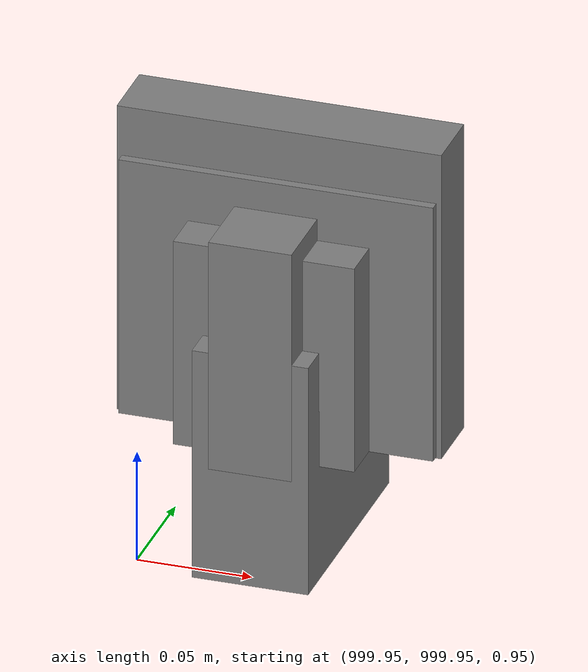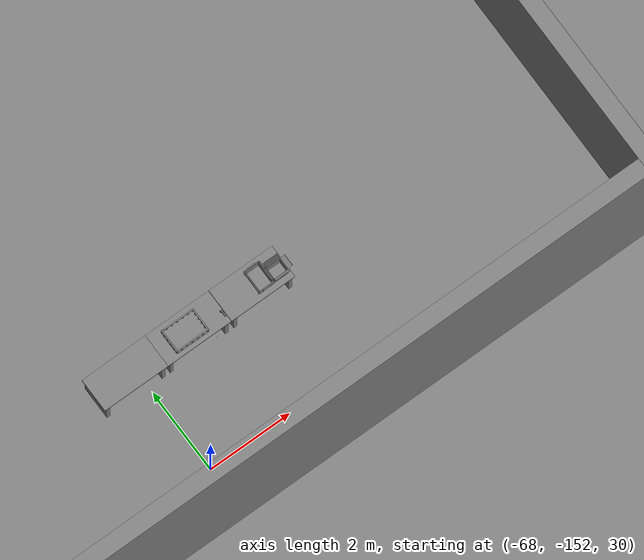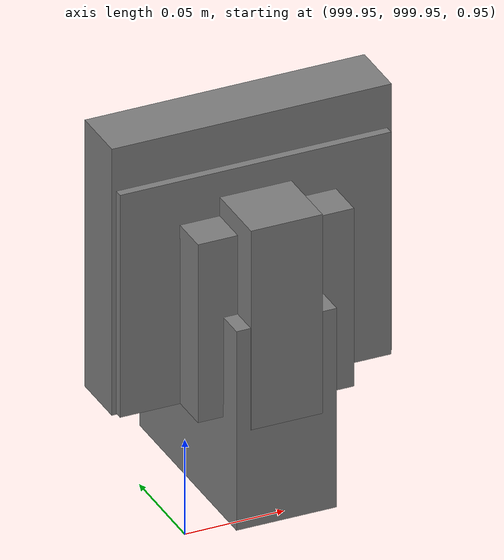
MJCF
<mujoco>
    <option gravity="0.000000000 0.000000000 -9.810000420" timestep="0.0049999999" integrator="implicitfast" density="1.225" viscosity="1.8000001e-05" noslip_iterations="10" iterations="100" sdf_iterations="50">
        <flag multiccd="disable"/>
    </option>
    <size memory="1000M"/>
    <compiler coordinate="local"/>
    <worldbody>
        <light cutoff="30" pos="0 1 1" dir="0 -1 -2"/>
        <light cutoff="30" pos="0 -1 1" dir="0 1 -2"/>
        <body pos="-64.866622925 -149.383972168 30.183746338" euler="89.999984741 89.999946594 0.000000000" name="openloong_gripper_2f85_fix_base_usda_bluebox_01">
            <geom contype="1" conaffinity="1" density="1000" type="box" material="" rgba="0.500000000 0.500000000 0.500000000 1.000000000" solimp="0.899999976 0.949999988 0.001000000" friction="1.000000000 0.005000000 0.000100000" solref="0.020000000 1.000000000" margin="0" condim="3" group="0" pos="0.276580811 0.187225342 0.000068665" quat="0.707106948 0.000077471 0.707106352 0.000077486" size="0.100000001 0.057999998 0.010000000" name="openloong_gripper_2f85_fix_base_usda_geom_071D53D5_6E75_4C9F_8D15_46ADDB390C82"/>
            <geom contype="1" conaffinity="1" density="1000" type="box" material="" rgba="0.500000000 0.500000000 0.500000000 1.000000000" solimp="0.899999976 0.949999988 0.001000000" friction="1.000000000 0.005000000 0.000100000" solref="0.020000000 1.000000000" margin="0" condim="3" group="0" pos="0.000000000 0.002883911 0.000000000" quat="0.999999881 0.000000000 0.000000000 0.000000000" size="0.254000008 0.003000000 0.172000006" name="openloong_gripper_2f85_fix_base_usda_geom_AF9717AE_68E0_415B_8AA7_F6E98DC0BE19"/>
            <geom contype="1" conaffinity="1" density="1000" type="box" material="" rgba="0.500000000 0.500000000 0.500000000 1.000000000" solimp="0.899999976 0.949999988 0.001000000" friction="1.000000000 0.005000000 0.000100000" solref="0.020000000 1.000000000" margin="0" condim="3" group="0" pos="0.000000000 0.124874115 0.173484802" quat="0.999796331 0.020176515 -0.000000015 0.000000030" size="0.259999990 0.119999997 0.007000000" name="openloong_gripper_2f85_fix_base_usda_geom_308ED225_85CA_40CD_B107_379C4222FBEA"/>
            <geom contype="1" conaffinity="1" density="1000" type="box" material="" rgba="0.500000000 0.500000000 0.500000000 1.000000000" solimp="0.899999976 0.949999988 0.001000000" friction="1.000000000 0.005000000 0.000100000" solref="0.020000000 1.000000000" margin="0" condim="3" group="0" pos="0.000000000 0.124874115 -0.173469543" quat="0.999796331 -0.020176545 -0.000000015 0.000000000" size="0.259999990 0.119999997 0.007000000" name="openloong_gripper_2f85_fix_base_usda_geom_B3967F5C_5A24_40D8_8ECB_67C33EE70F91"/>
            <geom contype="1" conaffinity="1" density="1000" type="box" material="" rgba="0.500000000 0.500000000 0.500000000 1.000000000" solimp="0.899999976 0.949999988 0.001000000" friction="1.000000000 0.005000000 0.000100000" solref="0.020000000 1.000000000" margin="0" condim="3" group="0" pos="0.000000000 0.214008331 0.188980103" quat="0.999912977 0.013176724 0.000000015 0.000000000" size="0.259999990 0.029999999 0.012500000" name="openloong_gripper_2f85_fix_base_usda_geom_13B6D27D_1DDE_4A5A_97E7_37122560784B"/>
            <geom contype="1" conaffinity="1" density="1000" type="box" material="" rgba="0.500000000 0.500000000 0.500000000 1.000000000" solimp="0.899999976 0.949999988 0.001000000" friction="1.000000000 0.005000000 0.000100000" solref="0.020000000 1.000000000" margin="0" condim="3" group="0" pos="-0.258361816 0.125289917 0.001876831" quat="0.702796936 -0.020792112 0.710783124 0.020769298" size="0.189999998 0.119999997 0.009000000" name="openloong_gripper_2f85_fix_base_usda_geom_25B5E140_F73F_4FD3_96B3_014A7E342625"/>
            <geom contype="1" conaffinity="1" density="1000" type="box" material="" rgba="0.500000000 0.500000000 0.500000000 1.000000000" solimp="0.899999976 0.949999988 0.001000000" friction="1.000000000 0.005000000 0.000100000" solref="0.020000000 1.000000000" margin="0" condim="3" group="0" pos="0.000000000 0.214008331 -0.188980103" quat="0.999912977 -0.013176769 0.000000030 0.000000015" size="0.259999990 0.029999999 0.012500000" name="openloong_gripper_2f85_fix_base_usda_geom_346ACD1D_F8E5_44CC_B017_5DAC392C1CCD"/>
            <geom contype="1" conaffinity="1" density="1000" type="box" material="" rgba="0.500000000 0.500000000 0.500000000 1.000000000" solimp="0.899999976 0.949999988 0.001000000" friction="1.000000000 0.005000000 0.000100000" solref="0.020000000 1.000000000" margin="0" condim="3" group="0" pos="-0.276611328 0.187225342 0.000068665" quat="0.707106650 0.000077441 0.707106709 0.000077456" size="0.100000001 0.057999998 0.010000000" name="openloong_gripper_2f85_fix_base_usda_geom_FE748388_1BFA_41D3_B8C1_35EC46D4381A"/>
            <geom contype="1" conaffinity="1" density="1000" type="box" material="" rgba="0.500000000 0.500000000 0.500000000 1.000000000" solimp="0.899999976 0.949999988 0.001000000" friction="1.000000000 0.005000000 0.000100000" solref="0.020000000 1.000000000" margin="0" condim="3" group="0" pos="0.258331299 0.125289917 0.001876831" quat="0.702851415 0.018856421 0.710823774 -0.019329369" size="0.189999998 0.119999997 0.009000000" name="openloong_gripper_2f85_fix_base_usda_geom_1A267693_87B2_42A5_87F4_A14A2853063F"/>
            <freejoint name="openloong_gripper_2f85_fix_base_usda_bluebox_01_joint"/>
            <site size="0.005000000 0.005000000 0.005000000" rgba="0.500000000 0.500000000 0.500000000 1.000000000" pos="0.000000000 0.000000000 0.000000000" quat="0.999961913 0.008726534 0.000000000 0.000000000" group="0" type="sphere" name="openloong_gripper_2f85_fix_base_usda_bluebox_01site"/>
        </body>
        <body pos="-64.496299744 -149.491867065 30.235729218" euler="0.000000000 0.000000000 89.999946594" name="openloong_gripper_2f85_fix_base_usda_cardboardbox_01">
            <geom contype="1" conaffinity="1" density="1000" type="box" material="" rgba="0.500000000 0.500000000 0.500000000 1.000000000" solimp="0.899999976 0.949999988 0.001000000" friction="1.000000000 0.005000000 0.000100000" solref="0.020000000 1.000000000" margin="0" condim="3" group="0" pos="-0.003166199 -0.004086494 0.005052090" quat="1.000000000 0.000000000 0.000000000 0.000000000" size="0.142499998 0.177500010 0.005000000" name="openloong_gripper_2f85_fix_base_usda_geom_C75E7FC0_C5BE_46DC_876E_C0B7A58B8F8E"/>
            <geom contype="1" conaffinity="1" density="1000" type="box" material="" rgba="0.500000000 0.500000000 0.500000000 1.000000000" solimp="0.899999976 0.949999988 0.001000000" friction="1.000000000 0.005000000 0.000100000" solref="0.020000000 1.000000000" margin="0" condim="3" group="0" pos="-0.003166199 0.170316696 0.150570869" quat="1.000000000 0.000000000 0.000000000 0.000000000" size="0.142499998 0.005000000 0.149999991" name="openloong_gripper_2f85_fix_base_usda_geom_E78C3A7A_0C46_4F82_B189_38BB42F9D928"/>
            <geom contype="1" conaffinity="1" density="1000" type="box" material="" rgba="0.500000000 0.500000000 0.500000000 1.000000000" solimp="0.899999976 0.949999988 0.001000000" friction="1.000000000 0.005000000 0.000100000" solref="0.020000000 1.000000000" margin="0" condim="3" group="0" pos="-0.147399902 -0.005307198 0.150570869" quat="1.000000000 0.000000000 0.000000000 0.000000000" size="0.005000000 0.177500010 0.149999991" name="openloong_gripper_2f85_fix_base_usda_geom_E43E8282_93A9_4BD4_BF9A_50A509AC477B"/>
            <geom contype="1" conaffinity="1" density="1000" type="box" material="" rgba="0.500000000 0.500000000 0.500000000 1.000000000" solimp="0.899999976 0.949999988 0.001000000" friction="1.000000000 0.005000000 0.000100000" solref="0.020000000 1.000000000" margin="0" condim="3" group="0" pos="0.140275955 -0.005307198 0.150570869" quat="1.000000000 0.000000000 0.000000000 0.000000000" size="0.005000000 0.177500010 0.149999991" name="openloong_gripper_2f85_fix_base_usda_geom_0700288D_20B4_4FAA_A727_773A9487F6DB"/>
            <geom contype="1" conaffinity="1" density="1000" type="box" material="" rgba="0.500000000 0.500000000 0.500000000 1.000000000" solimp="0.899999976 0.949999988 0.001000000" friction="1.000000000 0.005000000 0.000100000" solref="0.020000000 1.000000000" margin="0" condim="3" group="0" pos="-0.003166199 -0.181550980 0.150570869" quat="1.000000000 0.000000000 0.000000000 0.000000000" size="0.142499998 0.005000000 0.149999991" name="openloong_gripper_2f85_fix_base_usda_geom_801436CF_5E92_4769_B494_A490B755ACAA"/>
            <freejoint name="openloong_gripper_2f85_fix_base_usda_cardboardbox_01_joint"/>
            <site size="0.005000000 0.005000000 0.005000000" rgba="0.500000000 0.500000000 0.500000000 1.000000000" pos="0.000000000 0.000000000 0.000000000" quat="0.999961913 0.008726535 0.000000000 0.000000000" group="0" type="sphere" name="openloong_gripper_2f85_fix_base_usda_site_202FDB3D_6EBC_4F66_A608_F27CD030D99B"/>
            <body pos="0.139160156 -0.004048347 0.301930904" euler="-179.999954224 49.383502960 179.999954224" name="openloong_gripper_2f85_fix_base_usda_A1_006">
                <geom contype="1" conaffinity="1" density="1000" type="box" material="" rgba="0.500000000 0.500000000 0.500000000 1.000000000" solimp="0.899999976 0.949999988 0.001000000" friction="1.000000000 0.005000000 0.000100000" solref="0.020000000 1.000000000" margin="0" condim="3" group="0" pos="-0.071587563 0.000009537 0.001745224" quat="0.999999881 0.000000000 0.000000000 0.000000000" size="0.071249999 0.179999992 0.002500000" name="openloong_gripper_2f85_fix_base_usda_geom_3DC454CF_7365_42AB_A4CF_632ABE470A07"/>
                <joint armature="0" stiffness="0.07" damping="0.0099999998" axis="0.000000 1.000000 0.000000" type="hinge" name="openloong_gripper_2f85_fix_base_usda_A1_006"/>
            </body>
            <body pos="-0.145902634 -0.004086494 0.301938057" euler="-180.000000000 -60.000011444 -180.000000000" name="openloong_gripper_2f85_fix_base_usda_A2_006">
                <geom contype="1" conaffinity="1" density="1000" type="box" material="" rgba="0.500000000 0.500000000 0.500000000 1.000000000" solimp="0.899999976 0.949999988 0.001000000" friction="1.000000000 0.005000000 0.000100000" solref="0.020000000 1.000000000" margin="0" condim="3" group="0" pos="0.071268082 0.000009537 0.002717972" quat="0.000002921 0.000000000 -0.000000030 0.999999881" size="0.071249999 0.179999992 0.002500000" name="openloong_gripper_2f85_fix_base_usda_geom_5B7B88C5_83DE_441B_817D_B5C198D66A25"/>
                <joint armature="0" stiffness="0.07" damping="0.0099999998" axis="0.000000 1.000000 0.000000" type="hinge" name="openloong_gripper_2f85_fix_base_usda_A2_006"/>
            </body>
            <body pos="-0.003385544 0.175991058 0.301930904" euler="-125.858116150 -0.000004561 0.000002331" name="openloong_gripper_2f85_fix_base_usda_B2_006">
                <geom contype="1" conaffinity="1" density="1000" type="box" material="" rgba="0.500000000 0.500000000 0.500000000 1.000000000" solimp="0.899999976 0.949999988 0.001000000" friction="1.000000000 0.005000000 0.000100000" solref="0.020000000 1.000000000" margin="0" condim="3" group="0" pos="0.000009537 -0.070939064 -0.002470016" quat="0.999614120 0.027776197 -0.000000015 0.000000030" size="0.137500003 0.064999998 0.005000000" name="openloong_gripper_2f85_fix_base_usda_geom_F4AFBAAB_0D4B_40D7_AD13_C61555C15EC8"/>
                <joint armature="0" stiffness="0.07" damping="0.0099999998" axis="1.000000 0.000000 0.000000" type="hinge" name="openloong_gripper_2f85_fix_base_usda_B2_006"/>
            </body>
            <body pos="-0.003385544 -0.184140205 0.301938057" euler="147.805557251 0.000000000 0.000000000" name="openloong_gripper_2f85_fix_base_usda_B1_006">
                <geom contype="1" conaffinity="1" density="1000" type="box" material="" rgba="0.500000000 0.500000000 0.500000000 1.000000000" solimp="0.899999976 0.949999988 0.001000000" friction="1.000000000 0.005000000 0.000100000" solref="0.020000000 1.000000000" margin="0" condim="3" group="0" pos="-0.000028610 0.070202351 -0.002703667" quat="0.999614179 -0.027776167 0.000000000 0.000000000" size="0.137500003 0.064999998 0.005000000" name="openloong_gripper_2f85_fix_base_usda_geom_DC87015E_1652_43CD_BA02_60BAC7F83108"/>
                <joint armature="0" stiffness="0.07" damping="0.0099999998" axis="1.000000 0.000000 0.000000" type="hinge" name="openloong_gripper_2f85_fix_base_usda_B1_006"/>
            </body>
        </body>
        <body pos="-65.882858276 -149.481979370 30.229999542" euler="-64.487716675 0.000000000 0.000000000" name="openloong_gripper_2f85_fix_base_usda_Barcode">
            <geom contype="1" conaffinity="1" density="1000" type="box" material="" rgba="0.500000000 0.500000000 0.500000000 1.000000000" solimp="0.899999976 0.949999988 0.001000000" friction="1.000000000 0.005000000 0.000100000" solref="0.020000000 1.000000000" margin="0" condim="3" group="0" pos="0.000000000 0.013038635 0.001419067" quat="0.000000000 0.000000000 0.000000000 1.000000119" size="0.034000002 0.010000000 0.017999999" name="openloong_gripper_2f85_fix_base_usda_geom_BD914041_5D66_48A2_A27E_33712AEC4CA3"/>
            <geom contype="1" conaffinity="1" density="1000" type="box" material="" rgba="0.500000000 0.500000000 0.500000000 1.000000000" solimp="0.899999976 0.949999988 0.001000000" friction="1.000000000 0.005000000 0.000100000" solref="0.020000000 1.000000000" margin="0" condim="3" group="0" pos="0.000000000 -0.035301208 -0.007095337" quat="0.000000000 0.000000000 -0.043619365 0.999048233" size="0.028999999 0.010000000 0.020000000" name="openloong_gripper_2f85_fix_base_usda_geom_27B23A14_4A31_492B_8AFF_9F1DD09734D9"/>
            <geom contype="1" conaffinity="1" density="1000" type="box" material="" rgba="0.500000000 0.500000000 0.500000000 1.000000000" solimp="0.899999976 0.949999988 0.001000000" friction="1.000000000 0.005000000 0.000100000" solref="0.020000000 1.000000000" margin="0" condim="3" group="0" pos="0.000000000 -0.043411255 -0.011749268" quat="0.922262907 0.386563420 0.000000000 0.000000000" size="0.026000001 0.010000000 0.020000000" name="openloong_gripper_2f85_fix_base_usda_geom_C53E1CBF_1CB8_4916_AB3D_3D3EDF590D9E"/>
            <geom contype="1" conaffinity="1" density="1000" type="box" material="" rgba="0.500000000 0.500000000 0.500000000 1.000000000" solimp="0.899999976 0.949999988 0.001000000" friction="1.000000000 0.005000000 0.000100000" solref="0.020000000 1.000000000" margin="0" condim="3" group="0" pos="0.000000000 -0.016967773 -0.031860352" quat="0.000000000 0.000000000 0.000000000 1.000000119" size="0.008000000 0.010000000 0.013000000" name="openloong_gripper_2f85_fix_base_usda_geom_5846E667_B4D9_44D7_B02F_D4406ABB06CF"/>
            <geom contype="1" conaffinity="1" density="1000" type="box" material="" rgba="0.500000000 0.500000000 0.500000000 1.000000000" solimp="0.899999976 0.949999988 0.001000000" friction="1.000000000 0.005000000 0.000100000" solref="0.020000000 1.000000000" margin="0" condim="3" group="0" pos="0.000000000 -0.001869202 0.000312805" quat="0.953716993 0.300705761 0.000000000 0.000000000" size="0.032000002 0.010000000 0.018999999" name="openloong_gripper_2f85_fix_base_usda_geom_08BAB132_99A8_4D68_B84B_3FF5649F9348"/>
            <geom contype="1" conaffinity="1" density="1000" type="box" material="" rgba="0.500000000 0.500000000 0.500000000 1.000000000" solimp="0.899999976 0.949999988 0.001000000" friction="1.000000000 0.005000000 0.000100000" solref="0.020000000 1.000000000" margin="0" condim="3" group="0" pos="0.000000000 -0.019531250 -0.003173828" quat="0.953716993 0.300705761 0.000000000 0.000000000" size="0.030999999 0.010000000 0.020000000" name="openloong_gripper_2f85_fix_base_usda_geom_13CD33B9_B848_4F64_9C27_B5B56BDEEBF0"/>
            <geom contype="1" conaffinity="1" density="1000" type="box" material="" rgba="0.500000000 0.500000000 0.500000000 1.000000000" solimp="0.899999976 0.949999988 0.001000000" friction="1.000000000 0.005000000 0.000100000" solref="0.020000000 1.000000000" margin="0" condim="3" group="0" pos="0.000000000 -0.035301208 -0.007095337" quat="0.953716993 0.300705761 0.000000000 0.000000000" size="0.028999999 0.010000000 0.020000000" name="openloong_gripper_2f85_fix_base_usda_geom_A2A3851E_F8CB_4FB8_ABAF_B248CA90322F"/>
            <geom contype="1" conaffinity="1" density="1000" type="box" material="" rgba="0.500000000 0.500000000 0.500000000 1.000000000" solimp="0.899999976 0.949999988 0.001000000" friction="1.000000000 0.005000000 0.000100000" solref="0.020000000 1.000000000" margin="0" condim="3" group="0" pos="0.000000000 -0.042617798 -0.071121216" quat="0.000000000 0.000000000 0.000000000 1.000000119" size="0.013000000 0.021000000 0.059999999" name="openloong_gripper_2f85_fix_base_usda_geom_26903502_85CF_4B1C_AB9E_C1672538F0C2"/>
            <freejoint name="openloong_gripper_2f85_fix_base_usda_Barcode_joint"/>
            <site size="0.005000000 0.005000000 0.005000000" rgba="0.500000000 0.500000000 0.500000000 1.000000000" pos="0.000000000 0.000000000 0.000000000" quat="1.000000000 0.000000000 0.000000000 0.000000000" group="0" type="sphere" name="openloong_gripper_2f85_fix_base_usda_Barcode_site"/>
        </body>
        <body pos="-66.745018005 -149.392349243 30.184000015" euler="0.000000000 0.000000000 89.999946594" name="[22332360084946]_Basket_01">
            <geom contype="1" conaffinity="1" density="1000" type="box" material="" rgba="0.500000000 0.500000000 0.500000000 1.000000000" solimp="0.899999976 0.949999988 0.001000000" friction="1.000000000 0.005000000 0.000100000" solref="0.020000000 1.000000000" margin="0" condim="3" group="0" pos="-0.052425385 0.389207840 0.089787483" quat="0.707107008 0.000000000 0.000000000 0.707106411" size="0.014249999 0.014249999 0.059999999" name="[22332360084946]_geom_2125D4A3_E51E_4F38_A3CA_B25046FF025E"/>
            <geom contype="1" conaffinity="1" density="1000" type="box" material="" rgba="0.500000000 0.500000000 0.500000000 1.000000000" solimp="0.899999976 0.949999988 0.001000000" friction="1.000000000 0.005000000 0.000100000" solref="0.020000000 1.000000000" margin="0" condim="3" group="0" pos="0.264015198 -0.133043289 0.089787483" quat="0.707107008 0.000000000 0.000000000 0.707106411" size="0.014249999 0.014249999 0.059999999" name="[22332360084946]_geom_FC48D9FB_0F76_4FD9_8D3F_F0597F84C6EE"/>
            <geom contype="1" conaffinity="1" density="1000" type="box" material="" rgba="0.500000000 0.500000000 0.500000000 1.000000000" solimp="0.899999976 0.949999988 0.001000000" friction="1.000000000 0.005000000 0.000100000" solref="0.020000000 1.000000000" margin="0" condim="3" group="0" pos="-0.264015198 -0.265548706 0.089793205" quat="0.707107008 0.000000000 0.000000000 0.707106411" size="0.014249999 0.014249999 0.059999999" name="[22332360084946]_geom_5DCC22DF_974A_477C_9E96_4FD9483FC36C"/>
            <geom contype="1" conaffinity="1" density="1000" type="box" material="" rgba="0.500000000 0.500000000 0.500000000 1.000000000" solimp="0.899999976 0.949999988 0.001000000" friction="1.000000000 0.005000000 0.000100000" solref="0.020000000 1.000000000" margin="0" condim="3" group="0" pos="-0.160263062 -0.389322281 0.089793205" quat="0.707107008 0.000000000 0.000000000 0.707106411" size="0.014249999 0.014249999 0.059999999" name="[22332360084946]_geom_CD194F43_7F84_4BB4_BBAA_5BB322DF1451"/>
            <geom contype="1" conaffinity="1" density="1000" type="box" material="" rgba="0.500000000 0.500000000 0.500000000 1.000000000" solimp="0.899999976 0.949999988 0.001000000" friction="1.000000000 0.005000000 0.000100000" solref="0.020000000 1.000000000" margin="0" condim="3" group="0" pos="0.162265778 -0.389322281 0.089787483" quat="0.707107008 0.000000000 0.000000000 0.707106411" size="0.014249999 0.014249999 0.059999999" name="[22332360084946]_geom_2E3FB815_2E04_4037_82FA_EE12B3BA9E2D"/>
            <geom contype="1" conaffinity="1" density="1000" type="box" material="" rgba="0.500000000 0.500000000 0.500000000 1.000000000" solimp="0.899999976 0.949999988 0.001000000" friction="1.000000000 0.005000000 0.000100000" solref="0.020000000 1.000000000" margin="0" condim="3" group="0" pos="0.264015198 0.389207840 0.089787483" quat="0.707107008 0.000000000 0.000000000 0.707106411" size="0.014249999 0.014249999 0.059999999" name="[22332360084946]_geom_EDDDC0F8_F272_4E50_80BF_D3E3E97CF236"/>
            <geom contype="1" conaffinity="1" density="1000" type="box" material="" rgba="0.500000000 0.500000000 0.500000000 1.000000000" solimp="0.899999976 0.949999988 0.001000000" friction="1.000000000 0.005000000 0.000100000" solref="0.020000000 1.000000000" margin="0" condim="3" group="0" pos="-0.264015198 -0.133043289 0.089793205" quat="0.707107008 0.000000000 0.000000000 0.707106411" size="0.014249999 0.014249999 0.059999999" name="[22332360084946]_geom_3695E40D_80AB_4996_A8C0_D3AC7F027A72"/>
            <geom contype="1" conaffinity="1" density="1000" type="box" material="" rgba="0.500000000 0.500000000 0.500000000 1.000000000" solimp="0.899999976 0.949999988 0.001000000" friction="1.000000000 0.005000000 0.000100000" solref="0.020000000 1.000000000" margin="0" condim="3" group="0" pos="-0.264026642 0.269256592 0.089793205" quat="0.707107008 0.000000000 0.000000000 0.707106411" size="0.014249999 0.014249999 0.059999999" name="[22332360084946]_geom_63F14781_4400_4507_9196_81F5B0D4AD6C"/>
            <geom contype="1" conaffinity="1" density="1000" type="box" material="" rgba="0.500000000 0.500000000 0.500000000 1.000000000" solimp="0.899999976 0.949999988 0.001000000" friction="1.000000000 0.005000000 0.000100000" solref="0.020000000 1.000000000" margin="0" condim="3" group="0" pos="0.054462433 0.389207840 0.089787483" quat="0.707107008 0.000000000 0.000000000 0.707106411" size="0.014249999 0.014249999 0.059999999" name="[22332360084946]_geom_A73DE00B_C620_4C45_A5F5_42C30D3C6376"/>
            <geom contype="1" conaffinity="1" density="1000" type="box" material="" rgba="0.500000000 0.500000000 0.500000000 1.000000000" solimp="0.899999976 0.949999988 0.001000000" friction="1.000000000 0.005000000 0.000100000" solref="0.020000000 1.000000000" margin="0" condim="3" group="0" pos="0.054462433 -0.389322281 0.089787483" quat="0.707107008 0.000000000 0.000000000 0.707106411" size="0.014249999 0.014249999 0.059999999" name="[22332360084946]_geom_4764D144_8336_4B8E_B4D9_9BE5CC5312B9"/>
            <geom contype="1" conaffinity="1" density="1000" type="box" material="" rgba="0.500000000 0.500000000 0.500000000 1.000000000" solimp="0.899999976 0.949999988 0.001000000" friction="1.000000000 0.005000000 0.000100000" solref="0.020000000 1.000000000" margin="0" condim="3" group="0" pos="0.264015198 0.269256592 0.089793205" quat="0.707107008 0.000000000 0.000000000 0.707106411" size="0.014249999 0.014249999 0.059999999" name="[22332360084946]_geom_A8BCF49E_444B_4B6E_A707_F6EFEBDDAAFE"/>
            <geom contype="1" conaffinity="1" density="1000" type="box" material="" rgba="0.500000000 0.500000000 0.500000000 1.000000000" solimp="0.899999976 0.949999988 0.001000000" friction="1.000000000 0.005000000 0.000100000" solref="0.020000000 1.000000000" margin="0" condim="3" group="0" pos="0.264015198 -0.389322281 0.089787483" quat="0.707107008 0.000000000 0.000000000 0.707106411" size="0.014249999 0.014249999 0.059999999" name="[22332360084946]_geom_1CFE6B22_BCF8_402D_A173_CB2C6C7972B6"/>
            <geom contype="1" conaffinity="1" density="1000" type="box" material="" rgba="0.500000000 0.500000000 0.500000000 1.000000000" solimp="0.899999976 0.949999988 0.001000000" friction="1.000000000 0.005000000 0.000100000" solref="0.020000000 1.000000000" margin="0" condim="3" group="0" pos="0.000000000 0.000000000 0.015998840" quat="0.707107008 0.000000000 0.000000000 0.707106411" size="0.403499991 0.279000014 0.015750000" name="[22332360084946]_geom_EF499470_C53E_4DB6_B32B_F2C0448AA018"/>
            <geom contype="1" conaffinity="1" density="1000" type="box" material="" rgba="0.500000000 0.500000000 0.500000000 1.000000000" solimp="0.899999976 0.949999988 0.001000000" friction="1.000000000 0.005000000 0.000100000" solref="0.020000000 1.000000000" margin="0" condim="3" group="0" pos="0.000000000 -0.389476776 0.163619041" quat="0.707107008 0.000000000 0.000000000 0.707106411" size="0.015000000 0.277500004 0.015750000" name="[22332360084946]_geom_A2FCF2A6_FCEB_4BE9_B60F_D21711B4DFD7"/>
            <geom contype="1" conaffinity="1" density="1000" type="box" material="" rgba="0.500000000 0.500000000 0.500000000 1.000000000" solimp="0.899999976 0.949999988 0.001000000" friction="1.000000000 0.005000000 0.000100000" solref="0.020000000 1.000000000" margin="0" condim="3" group="0" pos="0.162265778 0.389207840 0.089787483" quat="0.707107008 0.000000000 0.000000000 0.707106411" size="0.014249999 0.014249999 0.059999999" name="[22332360084946]_geom_80EF2721_6FCD_4731_8203_5EA3D32A2DD0"/>
            <geom contype="1" conaffinity="1" density="1000" type="box" material="" rgba="0.500000000 0.500000000 0.500000000 1.000000000" solimp="0.899999976 0.949999988 0.001000000" friction="1.000000000 0.005000000 0.000100000" solref="0.020000000 1.000000000" margin="0" condim="3" group="0" pos="0.000000000 0.389471054 0.163619041" quat="0.707107008 0.000000000 0.000000000 0.707106411" size="0.015000000 0.277500004 0.015750000" name="[22332360084946]_geom_09892ADB_6BC3_4666_AB55_C86E0C4D9C1C"/>
            <geom contype="1" conaffinity="1" density="1000" type="box" material="" rgba="0.500000000 0.500000000 0.500000000 1.000000000" solimp="0.899999976 0.949999988 0.001000000" friction="1.000000000 0.005000000 0.000100000" solref="0.020000000 1.000000000" margin="0" condim="3" group="0" pos="-0.263511658 0.000000000 0.163619041" quat="0.707107008 0.000000000 0.000000000 0.707106411" size="0.403499991 0.015000000 0.015750000" name="[22332360084946]_geom_8961439D_82E8_4B6F_97D6_DA79C117424F"/>
            <geom contype="1" conaffinity="1" density="1000" type="box" material="" rgba="0.500000000 0.500000000 0.500000000 1.000000000" solimp="0.899999976 0.949999988 0.001000000" friction="1.000000000 0.005000000 0.000100000" solref="0.020000000 1.000000000" margin="0" condim="3" group="0" pos="-0.264015198 0.141334534 0.089793205" quat="0.707107008 0.000000000 0.000000000 0.707106411" size="0.014249999 0.014249999 0.059999999" name="[22332360084946]_geom_4E804BD1_8B59_4DBC_9323_8F644E468536"/>
            <geom contype="1" conaffinity="1" density="1000" type="box" material="" rgba="0.500000000 0.500000000 0.500000000 1.000000000" solimp="0.899999976 0.949999988 0.001000000" friction="1.000000000 0.005000000 0.000100000" solref="0.020000000 1.000000000" margin="0" condim="3" group="0" pos="0.264015198 -0.265548706 0.089787483" quat="0.707107008 0.000000000 0.000000000 0.707106411" size="0.014249999 0.014249999 0.059999999" name="[22332360084946]_geom_F9FD577D_88CB_476A_8EB7_223DE5EDA6C5"/>
            <geom contype="1" conaffinity="1" density="1000" type="box" material="" rgba="0.500000000 0.500000000 0.500000000 1.000000000" solimp="0.899999976 0.949999988 0.001000000" friction="1.000000000 0.005000000 0.000100000" solref="0.020000000 1.000000000" margin="0" condim="3" group="0" pos="-0.160263062 0.389207840 0.089787483" quat="0.707107008 0.000000000 0.000000000 0.707106411" size="0.014249999 0.014249999 0.059999999" name="[22332360084946]_geom_B355691F_2C26_41CA_968D_1A8A3585B846"/>
            <geom contype="1" conaffinity="1" density="1000" type="box" material="" rgba="0.500000000 0.500000000 0.500000000 1.000000000" solimp="0.899999976 0.949999988 0.001000000" friction="1.000000000 0.005000000 0.000100000" solref="0.020000000 1.000000000" margin="0" condim="3" group="0" pos="-0.052425385 -0.389322281 0.089787483" quat="0.707107008 0.000000000 0.000000000 0.707106411" size="0.014249999 0.014249999 0.059999999" name="[22332360084946]_geom_E0FAD6C4_D76E_46FA_8518_93576037B378"/>
            <geom contype="1" conaffinity="1" density="1000" type="box" material="" rgba="0.500000000 0.500000000 0.500000000 1.000000000" solimp="0.899999976 0.949999988 0.001000000" friction="1.000000000 0.005000000 0.000100000" solref="0.020000000 1.000000000" margin="0" condim="3" group="0" pos="-0.264026642 -0.389322281 0.089793205" quat="0.707107008 0.000000000 0.000000000 0.707106411" size="0.014249999 0.014249999 0.059999999" name="[22332360084946]_geom_F85A3D86_FFF5_420E_8E8A_BE989402AA9B"/>
            <geom contype="1" conaffinity="1" density="1000" type="box" material="" rgba="0.500000000 0.500000000 0.500000000 1.000000000" solimp="0.899999976 0.949999988 0.001000000" friction="1.000000000 0.005000000 0.000100000" solref="0.020000000 1.000000000" margin="0" condim="3" group="0" pos="0.264015198 0.141334534 0.089787483" quat="0.707107008 0.000000000 0.000000000 0.707106411" size="0.014249999 0.014249999 0.059999999" name="[22332360084946]_geom_AB2A958C_F772_4989_9085_64F4B4C2543E"/>
            <geom contype="1" conaffinity="1" density="1000" type="box" material="" rgba="0.500000000 0.500000000 0.500000000 1.000000000" solimp="0.899999976 0.949999988 0.001000000" friction="1.000000000 0.005000000 0.000100000" solref="0.020000000 1.000000000" margin="0" condim="3" group="0" pos="-0.264015198 0.389207840 0.089793205" quat="0.707107008 0.000000000 0.000000000 0.707106411" size="0.014249999 0.014249999 0.059999999" name="[22332360084946]_geom_1EBB555E_7A9E_4A2F_A0F5_CBAF754C625F"/>
            <geom contype="1" conaffinity="1" density="1000" type="box" material="" rgba="0.500000000 0.500000000 0.500000000 1.000000000" solimp="0.899999976 0.949999988 0.001000000" friction="1.000000000 0.005000000 0.000100000" solref="0.020000000 1.000000000" margin="0" condim="3" group="0" pos="0.264015198 0.004480362 0.089787483" quat="0.707107008 0.000000000 0.000000000 0.707106411" size="0.014249999 0.014249999 0.059999999" name="[22332360084946]_geom_8BAC3C66_B2B4_4C4C_9F73_075F650886D1"/>
            <geom contype="1" conaffinity="1" density="1000" type="box" material="" rgba="0.500000000 0.500000000 0.500000000 1.000000000" solimp="0.899999976 0.949999988 0.001000000" friction="1.000000000 0.005000000 0.000100000" solref="0.020000000 1.000000000" margin="0" condim="3" group="0" pos="0.263694763 -0.000011444 0.163619041" quat="0.707107008 0.000000000 0.000000000 0.707106411" size="0.403499991 0.015000000 0.015750000" name="[22332360084946]_geom_2DA6C8DF_C676_411F_BC1A_C66F9AC076E7"/>
            <geom contype="1" conaffinity="1" density="1000" type="box" material="" rgba="0.500000000 0.500000000 0.500000000 1.000000000" solimp="0.899999976 0.949999988 0.001000000" friction="1.000000000 0.005000000 0.000100000" solref="0.020000000 1.000000000" margin="0" condim="3" group="0" pos="-0.264015198 0.004480362 0.089793205" quat="0.707107008 0.000000000 0.000000000 0.707106411" size="0.014249999 0.014249999 0.059999999" name="[22332360084946]_geom_CEF7B197_2358_40EA_A02F_C3AEAE8FD74C"/>
            <freejoint name="[22332360084946]_joint_68CC779B_E684_455B_8505_44FC613A27CD"/>
        </body>
        <body pos="0.000000000 0.000000000 0.000000000" euler="0.000000000 0.000000000 0.000000000" name="Static Objects_Static Objects">
            <geom contype="1" conaffinity="1" density="1000" type="box" material="" rgba="0.500000000 0.500000000 0.500000000 1.000000000" solimp="0.899999976 0.949999988 0.001000000" friction="1.000000000 0.005000000 0.000100000" solref="0.020000000 1.000000000" margin="0" condim="3" group="0" pos="-67.544113159 -149.365814209 29.727830887" quat="0.500000417 0.499999970 0.499999553 0.499999970" size="0.381000012 0.319999993 0.041000001" name="Static Objects_geom_50BA6033_166A_48FF_A8DD_EC4014967951"/>
            <geom contype="1" conaffinity="1" density="1000" type="box" material="" rgba="0.500000000 0.500000000 0.500000000 1.000000000" solimp="0.899999976 0.949999988 0.001000000" friction="1.000000000 0.005000000 0.000100000" solref="0.020000000 1.000000000" margin="0" condim="3" group="0" pos="-68.239501953 -149.365814209 30.086868286" quat="0.500000417 0.499999970 0.499999553 0.499999970" size="0.370999992 0.039500002 0.745000005" name="Static Objects_geom_7C9CF70C_2A36_446E_A862_327F057C28F3"/>
            <geom contype="1" conaffinity="1" density="1000" type="box" material="" rgba="0.500000000 0.500000000 0.500000000 1.000000000" solimp="0.899999976 0.949999988 0.001000000" friction="1.000000000 0.005000000 0.000100000" solref="0.020000000 1.000000000" margin="0" condim="3" group="0" pos="-68.239501953 -149.365814209 30.147235870" quat="0.500000417 0.499999970 0.499999553 0.499999970" size="0.400000006 0.022000000 0.800000012" name="Static Objects_geom_1EF1E24F_1238_4DC0_8C7D_5758DD452A01"/>
            <geom contype="1" conaffinity="1" density="1000" type="box" material="" rgba="0.500000000 0.500000000 0.500000000 1.000000000" solimp="0.899999976 0.949999988 0.001000000" friction="1.000000000 0.005000000 0.000100000" solref="0.020000000 1.000000000" margin="0" condim="3" group="0" pos="-68.934890747 -149.365814209 29.727830887" quat="0.500000417 0.499999970 0.499999553 0.499999970" size="0.381000012 0.319999993 0.041000001" name="Static Objects_geom_B3A14346_0CE1_4374_B102_49C8CB5687F1"/>
            <geom contype="1" conaffinity="1" density="1000" type="box" material="" rgba="0.500000000 0.500000000 0.500000000 1.000000000" solimp="0.899999976 0.949999988 0.001000000" friction="1.000000000 0.005000000 0.000100000" solref="0.020000000 1.000000000" margin="0" condim="3" group="0" pos="-68.239501953 -149.365814209 29.561563492" quat="0.500000417 0.499999970 0.499999553 0.499999970" size="0.020000000 0.022000000 0.660000026" name="Static Objects_geom_FA4A51EA_5E81_4A54_88A6_CD2431E37B7C"/>
            <geom contype="1" conaffinity="1" density="1000" type="box" material="" rgba="0.500000000 0.500000000 0.500000000 1.000000000" solimp="0.899999976 0.949999988 0.001000000" friction="1.000000000 0.005000000 0.000100000" solref="0.020000000 1.000000000" margin="0" condim="3" group="0" pos="-65.945671082 -149.365814209 29.727830887" quat="0.500000417 0.499999970 0.499999553 0.499999970" size="0.381000012 0.319999993 0.041000001" name="Static Objects_geom_5300615C_25FB_4B7C_ABF4_55E127179F1B"/>
            <geom contype="1" conaffinity="1" density="1000" type="box" material="" rgba="0.500000000 0.500000000 0.500000000 1.000000000" solimp="0.899999976 0.949999988 0.001000000" friction="1.000000000 0.005000000 0.000100000" solref="0.020000000 1.000000000" margin="0" condim="3" group="0" pos="-66.641059875 -149.365814209 30.086868286" quat="0.500000417 0.499999970 0.499999553 0.499999970" size="0.370999992 0.039500002 0.745000005" name="Static Objects_geom_F72DBBA5_A4E6_4423_83DD_BE0E1C2335E8"/>
            <geom contype="1" conaffinity="1" density="1000" type="box" material="" rgba="0.500000000 0.500000000 0.500000000 1.000000000" solimp="0.899999976 0.949999988 0.001000000" friction="1.000000000 0.005000000 0.000100000" solref="0.020000000 1.000000000" margin="0" condim="3" group="0" pos="-66.641059875 -149.365814209 30.147235870" quat="0.500000417 0.499999970 0.499999553 0.499999970" size="0.400000006 0.022000000 0.800000012" name="Static Objects_geom_E2B6F1AA_CDE5_49BF_8499_8E793762F3F4"/>
            <geom contype="1" conaffinity="1" density="1000" type="box" material="" rgba="0.500000000 0.500000000 0.500000000 1.000000000" solimp="0.899999976 0.949999988 0.001000000" friction="1.000000000 0.005000000 0.000100000" solref="0.020000000 1.000000000" margin="0" condim="3" group="0" pos="-67.336448669 -149.365814209 29.727830887" quat="0.500000417 0.499999970 0.499999553 0.499999970" size="0.381000012 0.319999993 0.041000001" name="Static Objects_geom_E5D04ADD_99F0_4EE0_854F_C7470BE669D4"/>
            <geom contype="1" conaffinity="1" density="1000" type="box" material="" rgba="0.500000000 0.500000000 0.500000000 1.000000000" solimp="0.899999976 0.949999988 0.001000000" friction="1.000000000 0.005000000 0.000100000" solref="0.020000000 1.000000000" margin="0" condim="3" group="0" pos="-66.641059875 -149.365814209 29.561563492" quat="0.500000417 0.499999970 0.499999553 0.499999970" size="0.020000000 0.022000000 0.660000026" name="Static Objects_geom_945FEBDF_6584_4FED_A109_0156404D0E37"/>
            <geom contype="1" conaffinity="1" density="1000" type="box" material="" rgba="0.500000000 0.500000000 0.500000000 1.000000000" solimp="0.899999976 0.949999988 0.001000000" friction="1.000000000 0.005000000 0.000100000" solref="0.020000000 1.000000000" margin="0" condim="3" group="0" pos="-64.338577271 -149.365814209 29.727830887" quat="0.500000417 0.499999970 0.499999553 0.499999970" size="0.381000012 0.319999993 0.041000001" name="Static Objects_geom_473602CD_D911_412B_9F57_C702F989D9D4"/>
            <geom contype="1" conaffinity="1" density="1000" type="box" material="" rgba="0.500000000 0.500000000 0.500000000 1.000000000" solimp="0.899999976 0.949999988 0.001000000" friction="1.000000000 0.005000000 0.000100000" solref="0.020000000 1.000000000" margin="0" condim="3" group="0" pos="-65.033966064 -149.365814209 30.086868286" quat="0.500000417 0.499999970 0.499999553 0.499999970" size="0.370999992 0.039500002 0.745000005" name="Static Objects_geom_35823A64_2E88_4E88_B584_2AEC49BE905A"/>
            <geom contype="1" conaffinity="1" density="1000" type="box" material="" rgba="0.500000000 0.500000000 0.500000000 1.000000000" solimp="0.899999976 0.949999988 0.001000000" friction="1.000000000 0.005000000 0.000100000" solref="0.020000000 1.000000000" margin="0" condim="3" group="0" pos="-65.033966064 -149.365814209 30.147235870" quat="0.500000417 0.499999970 0.499999553 0.499999970" size="0.400000006 0.022000000 0.800000012" name="Static Objects_geom_0C74CF57_D3E5_4EA5_8511_0FF70CE11A16"/>
            <geom contype="1" conaffinity="1" density="1000" type="box" material="" rgba="0.500000000 0.500000000 0.500000000 1.000000000" solimp="0.899999976 0.949999988 0.001000000" friction="1.000000000 0.005000000 0.000100000" solref="0.020000000 1.000000000" margin="0" condim="3" group="0" pos="-65.729354858 -149.365814209 29.727830887" quat="0.500000417 0.499999970 0.499999553 0.499999970" size="0.381000012 0.319999993 0.041000001" name="Static Objects_geom_31171E1E_62A5_4737_BB5C_6E304FAFE69B"/>
            <geom contype="1" conaffinity="1" density="1000" type="box" material="" rgba="0.500000000 0.500000000 0.500000000 1.000000000" solimp="0.899999976 0.949999988 0.001000000" friction="1.000000000 0.005000000 0.000100000" solref="0.020000000 1.000000000" margin="0" condim="3" group="0" pos="-65.033966064 -149.365814209 29.561563492" quat="0.500000417 0.499999970 0.499999553 0.499999970" size="0.020000000 0.022000000 0.660000026" name="Static Objects_geom_7536FF25_A99F_4098_8F0C_6DC7035DD9CA"/>
            <geom contype="1" conaffinity="1" density="1000" type="box" material="" rgba="0.500000000 0.500000000 0.500000000 1.000000000" solimp="0.899999976 0.949999988 0.001000000" friction="1.000000000 0.005000000 0.000100000" solref="0.020000000 1.000000000" margin="0" condim="3" group="0" pos="-61.754566193 -137.853729248 33.906845093" quat="0.707107067 0.000000000 0.000000000 0.707106471" size="0.759999990 0.759999990 4.500000000" name="Static Objects_geom_F7AF67D3_3B3B_405D_91CE_FD016CD9C0AE"/>
            <geom contype="1" conaffinity="1" density="1000" type="box" material="" rgba="0.500000000 0.500000000 0.500000000 1.000000000" solimp="0.899999976 0.949999988 0.001000000" friction="1.000000000 0.005000000 0.000100000" solref="0.020000000 1.000000000" margin="0" condim="3" group="0" pos="-57.511135101 -144.927108765 31.707921982" quat="1.000000000 0.000000000 0.000000000 0.000000000" size="0.200000003 8.000000000 2.299999952" name="Static Objects_geom_D565FC7C_1F41_4313_81ED_4EFA97288838"/>
            <geom contype="1" conaffinity="1" density="1000" type="box" material="" rgba="0.500000000 0.500000000 0.500000000 1.000000000" solimp="0.899999976 0.949999988 0.001000000" friction="1.000000000 0.005000000 0.000100000" solref="0.020000000 1.000000000" margin="0" condim="3" group="0" pos="-80.517646790 -157.574050903 31.688196182" quat="0.707107067 0.000000000 0.000000000 0.707106471" size="0.600000024 0.600000024 2.299999952" name="Static Objects_geom_44A8098F_47E4_4201_A174_C5F25DFB1FF2"/>
            <geom contype="1" conaffinity="1" density="1000" type="box" material="" rgba="0.500000000 0.500000000 0.500000000 1.000000000" solimp="0.899999976 0.949999988 0.001000000" friction="1.000000000 0.005000000 0.000100000" solref="0.020000000 1.000000000" margin="0" condim="3" group="0" pos="-80.711044312 -147.414932251 31.666158676" quat="1.000000000 0.000000000 0.000000000 0.000000000" size="0.200000003 10.000000000 2.299999952" name="Static Objects_geom_8454C45D_01F9_45EC_917D_1EBCC074CA66"/>
            <geom contype="1" conaffinity="1" density="1000" type="box" material="" rgba="0.500000000 0.500000000 0.500000000 1.000000000" solimp="0.899999976 0.949999988 0.001000000" friction="1.000000000 0.005000000 0.000100000" solref="0.020000000 1.000000000" margin="0" condim="3" group="0" pos="-57.687217712 -137.434692383 31.688196182" quat="0.707107067 0.000000000 0.000000000 0.707106471" size="0.600000024 0.600000024 2.299999952" name="Static Objects_geom_1257FB77_4425_4568_B3C4_E9ACCE07E788"/>
            <geom contype="1" conaffinity="1" density="1000" type="box" material="" rgba="0.500000000 0.500000000 0.500000000 1.000000000" solimp="0.899999976 0.949999988 0.001000000" friction="1.000000000 0.005000000 0.000100000" solref="0.020000000 1.000000000" margin="0" condim="3" group="0" pos="-69.537033081 -140.263229370 31.714921951" quat="0.707107067 0.000000000 0.000000000 0.707106471" size="0.759999990 4.500000000 2.299999952" name="Static Objects_geom_984B483F_1FB7_44F1_93F4_1F6F61CE651F"/>
            <geom contype="1" conaffinity="1" density="1000" type="box" material="" rgba="0.500000000 0.500000000 0.500000000 1.000000000" solimp="0.899999976 0.949999988 0.001000000" friction="1.000000000 0.005000000 0.000100000" solref="0.020000000 1.000000000" margin="0" condim="3" group="0" pos="-80.073638916 -137.853713989 33.906845093" quat="0.707107067 0.000000000 0.000000000 0.707106471" size="0.759999990 0.759999990 4.500000000" name="Static Objects_geom_3D49ACC3_FFF2_417F_A44B_7D1478ED4261"/>
            <geom contype="1" conaffinity="1" density="1000" type="box" material="" rgba="0.500000000 0.500000000 0.500000000 1.000000000" solimp="0.899999976 0.949999988 0.001000000" friction="1.000000000 0.005000000 0.000100000" solref="0.020000000 1.000000000" margin="0" condim="3" group="0" pos="-73.406707764 -155.734664917 31.707921982" quat="1.000000000 0.000000000 0.000000000 0.000000000" size="0.200000003 3.000000000 2.299999952" name="Static Objects_geom_D3480C8F_45E3_4F38_A217_719D29F084FF"/>
            <geom contype="1" conaffinity="1" density="1000" type="box" material="" rgba="0.500000000 0.500000000 0.500000000 1.000000000" solimp="0.899999976 0.949999988 0.001000000" friction="1.000000000 0.005000000 0.000100000" solref="0.020000000 1.000000000" margin="0" condim="3" group="0" pos="-68.497543335 -137.448257446 31.707921982" quat="0.707107067 0.000000000 0.000000000 0.707106471" size="0.200000003 14.000000000 2.299999952" name="Static Objects_geom_D1D47EF5_DAEB_4D8F_A4BA_7F6A26C0A1EC"/>
            <geom contype="1" conaffinity="1" density="1000" type="cylinder" material="" rgba="0.500000000 0.500000000 0.500000000 1.000000000" solimp="0.899999976 0.949999988 0.001000000" friction="1.000000000 0.005000000 0.000100000" solref="0.020000000 1.000000000" margin="0" condim="3" group="0" pos="-68.868522644 -142.134506226 31.711090088" quat="0.707107067 0.000000000 0.000000000 0.707106471" size="0.509999990 2.299999952 1.000000000" name="Static Objects_geom_E65BA69F_72A2_4D09_B603_BC13C8F06987"/>
            <geom contype="1" conaffinity="1" density="1000" type="plane" material="" rgba="0.500000000 0.500000000 0.500000000 1.000000000" solimp="0.899999976 0.949999988 0.001000000" friction="1.000000000 0.005000000 0.000100000" solref="0.020000000 1.000000000" margin="0" condim="3" group="0" pos="-72.873703003 -147.131927490 29.409669876" quat="1.000000000 0.000000000 0.000000000 0.000000000" size="18.000000000 14.000000000 1.000000000" name="Static Objects_geom_B2BCA798_D153_4781_92C7_DF7EB8E818C5"/>
            <geom contype="1" conaffinity="1" density="1000" type="box" material="" rgba="0.500000000 0.500000000 0.500000000 1.000000000" solimp="0.899999976 0.949999988 0.001000000" friction="1.000000000 0.005000000 0.000100000" solref="0.020000000 1.000000000" margin="0" condim="3" group="0" pos="-79.943580627 -157.782272339 31.707921982" quat="0.707107067 0.000000000 0.000000000 0.707106471" size="0.200000003 7.000000000 2.299999952" name="Static Objects_geom_8F1C1494_CA7D_4ADD_A4E3_85E1EBE0409E"/>
            <geom contype="1" conaffinity="1" density="1000" type="box" material="" rgba="0.500000000 0.500000000 0.500000000 1.000000000" solimp="0.899999976 0.949999988 0.001000000" friction="1.000000000 0.005000000 0.000100000" solref="0.020000000 1.000000000" margin="0" condim="3" group="0" pos="-65.421028137 -152.903442383 31.707921982" quat="0.707107067 0.000000000 0.000000000 0.707106471" size="0.200000003 7.800000191 2.299999952" name="Static Objects_geom_8A876DBD_13E7_4FF3_9A21_52E99A52E2FA"/>
            <geom contype="1" conaffinity="1" density="1000" type="box" material="" rgba="0.500000000 0.500000000 0.500000000 1.000000000" solimp="0.899999976 0.949999988 0.001000000" friction="1.000000000 0.005000000 0.000100000" solref="0.020000000 1.000000000" margin="0" condim="3" group="0" pos="-74.776908875 -149.964416504 31.688196182" quat="1.000000000 0.000000000 0.000000000 0.000000000" size="0.600000024 0.409999996 2.299999952" name="Static Objects_geom_09B332C3_1809_4137_8117_FB079E751022"/>
            <geom contype="1" conaffinity="1" density="1000" type="cylinder" material="" rgba="0.500000000 0.500000000 0.500000000 1.000000000" solimp="0.899999976 0.949999988 0.001000000" friction="1.000000000 0.005000000 0.000100000" solref="0.020000000 1.000000000" margin="0" condim="3" group="0" pos="-60.161884308 -142.134506226 31.711090088" quat="0.707107067 0.000000000 0.000000000 0.707106471" size="0.509999990 2.299999952 1.000000000" name="Static Objects_geom_59FFE9C8_B8F5_43E6_B67B_5DEE56782419"/>
            <geom contype="1" conaffinity="1" density="1000" type="cylinder" material="" rgba="0.500000000 0.500000000 0.500000000 1.000000000" solimp="0.899999976 0.949999988 0.001000000" friction="1.000000000 0.005000000 0.000100000" solref="0.020000000 1.000000000" margin="0" condim="3" group="0" pos="-75.382453918 -149.963455200 31.711090088" quat="0.707107067 0.000000000 0.000000000 0.707106471" size="0.409999996 2.299999952 1.000000000" name="Static Objects_geom_4B388526_FB74_4EDA_834F_B0DD64FF0B28"/>
            <geom contype="1" conaffinity="1" density="1000" type="cylinder" material="" rgba="0.500000000 0.500000000 0.500000000 1.000000000" solimp="0.899999976 0.949999988 0.001000000" friction="1.000000000 0.005000000 0.000100000" solref="0.020000000 1.000000000" margin="0" condim="3" group="0" pos="-74.154960632 -149.963455200 31.711090088" quat="0.707107067 0.000000000 0.000000000 0.707106471" size="0.409999996 2.299999952 1.000000000" name="Static Objects_geom_40116F06_C0F7_4950_AD03_EA34E2E25A58"/>
            <geom contype="1" conaffinity="1" density="1000" type="cylinder" material="" rgba="0.500000000 0.500000000 0.500000000 1.000000000" solimp="0.899999976 0.949999988 0.001000000" friction="1.000000000 0.005000000 0.000100000" solref="0.020000000 1.000000000" margin="0" condim="3" group="0" pos="-77.566612244 -142.134506226 31.711090088" quat="0.707107067 0.000000000 0.000000000 0.707106471" size="0.509999990 2.299999952 1.000000000" name="Static Objects_geom_55B55C2D_6A07_4E47_BD27_9ECC263D5C40"/>
        </body>
        <body pos="1000.000000000 1000.000000000 1.000000000" euler="0.000000000 0.000000000 180.000000000" name="openloong_gripper_2f85_fix_base_usda_cpu_fan">
            <geom contype="1" conaffinity="1" density="1000" type="box" material="" rgba="0.500000000 0.500000000 0.500000000 1.000000000" solimp="0.899999976 0.949999988 0.001000000" friction="1.000000000 0.005000000 0.000100000" solref="0.020000000 1.000000000" margin="0" condim="3" group="0" pos="0.000000000 0.000000000 0.070034981" quat="0.000000000 0.000000000 0.000000000 1.000000000" size="0.070700005 0.014699999 0.070700005" name="openloong_gripper_2f85_fix_base_usda_geom_11225458_B766_40D5_9DD0_5779846A2E17"/>
            <freejoint name="openloong_gripper_2f85_fix_base_usda_cpu_fan_joint"/>
            <site size="0.005000000 0.005000000 0.005000000" rgba="0.500000000 0.500000000 0.500000000 1.000000000" pos="0.000000000 0.000000000 0.000000000" quat="0.999961913 0.008726535 0.000000000 0.000000000" group="0" type="sphere" name="openloong_gripper_2f85_fix_base_usda_cpu_fancsite"/>
        </body>
        <body pos="1000.000000000 1000.000000000 1.000000000" euler="0.000000000 0.000000000 180.000000000" name="openloong_gripper_2f85_fix_base_usda_wifi_box">
            <geom contype="1" conaffinity="1" density="1000" type="box" material="" rgba="0.500000000 0.500000000 0.500000000 1.000000000" solimp="0.899999976 0.949999988 0.001000000" friction="1.000000000 0.005000000 0.000100000" solref="0.020000000 1.000000000" margin="0" condim="3" group="0" pos="0.000000000 0.000000000 0.058978677" quat="0.000000000 0.000000047 0.000000000 1.000000000" size="0.068499997 0.018999999 0.059000000" name="openloong_gripper_2f85_fix_base_usda_geom_7384EB67_8B07_407E_8CAA_CB6414592995"/>
            <freejoint name="openloong_gripper_2f85_fix_base_usda_wifi_box_joint"/>
            <site size="0.005000000 0.005000000 0.005000000" rgba="0.500000000 0.500000000 0.500000000 1.000000000" pos="0.000000000 0.000000000 0.000000000" quat="0.999961913 0.008726500 0.000000000 0.000000000" group="0" type="sphere" name="openloong_gripper_2f85_fix_base_usda_wifi_boxsite"/>
        </body>
        <body pos="1000.000000000 1000.000000000 1.000000000" euler="0.000011953 0.000005123 -179.999984741" name="openloong_gripper_2f85_fix_base_usda_intel_box">
            <geom contype="1" conaffinity="1" density="1000" type="box" material="" rgba="0.500000000 0.500000000 0.500000000 1.000000000" solimp="0.899999976 0.949999988 0.001000000" friction="1.000000000 0.005000000 0.000100000" solref="0.020000000 1.000000000" margin="0" condim="3" group="0" pos="0.000000000 -0.000067139 0.000082284" quat="0.707106709 0.000000225 0.000000253 0.707106650" size="0.052800003 0.025300000 0.052800003" name="openloong_gripper_2f85_fix_base_usda_geom_D03B24F8_1430_4C9F_811B_8540900832C2"/>
            <freejoint name="openloong_gripper_2f85_fix_base_usda_intel_box_joint"/>
            <site size="0.005000000 0.005000000 0.005000000" rgba="0.500000000 0.500000000 0.500000000 1.000000000" pos="0.000000000 0.000000000 0.000000000" quat="0.999961913 0.008726500 0.000000000 0.000000000" group="0" type="sphere" name="openloong_gripper_2f85_fix_base_usda_intel_boxsite"/>
        </body>
        <body pos="-66.173561096 -149.588653564 31.164230347" euler="-151.406906128 43.613674164 16.889768600" mocap="true" name="spotlight2_SpotLight"/>
        <body pos="1000.000000000 999.999938965 1.000000000" euler="0.000000000 0.000000000 180.000000000" name="openloong_gripper_2f85_fix_base_usda_intelcore_i5">
            <geom contype="1" conaffinity="1" density="1000" type="box" material="" rgba="0.500000000 0.500000000 0.500000000 1.000000000" solimp="0.899999976 0.949999988 0.001000000" friction="1.000000000 0.005000000 0.000100000" solref="0.020000000 1.000000000" margin="0" condim="3" group="0" pos="0.000000000 0.000000000 0.051722717" quat="0.707106709 0.000000000 0.000000000 -0.707106769" size="0.052800000 0.018080002 0.052800000" name="openloong_gripper_2f85_fix_base_usda_geom_519681CB_217B_4DE6_B84C_E7A87E388464"/>
            <freejoint name="openloong_gripper_2f85_fix_base_usda_intelcore_i5_joint"/>
            <site size="0.005000000 0.005000000 0.005000000" rgba="0.500000000 0.500000000 0.500000000 1.000000000" pos="0.000000000 0.000000000 0.000000000" quat="0.999961913 0.008726534 0.000000000 0.000000000" group="0" type="sphere" name="openloong_gripper_2f85_fix_base_usda_intelcore_i5site"/>
        </body>
        <body pos="-65.915214539 -148.895812988 31.171823502" euler="121.029685974 26.412136078 135.924575806" mocap="true" name="spotlight3_SpotLight"/>
        <body pos="1000.000000000 1000.000000000 1.000000000" euler="0.000000000 0.000000000 180.000000000" name="openloong_gripper_2f85_fix_base_usda_battery_01">
            <geom contype="1" conaffinity="1" density="1000" type="box" material="" rgba="0.500000000 0.500000000 0.500000000 1.000000000" solimp="0.899999976 0.949999988 0.001000000" friction="1.000000000 0.005000000 0.000100000" solref="0.020000000 1.000000000" margin="0" condim="3" group="0" pos="-0.011123657 -0.041940309 0.101691343" quat="1.000000000 0.000000000 0.000000000 0.000000000" size="0.010800000 0.003375000 0.004725000" name="openloong_gripper_2f85_fix_base_usda_geom_D62184BA_85AB_4C3F_AA75_D3D1375809BF"/>
            <geom contype="1" conaffinity="1" density="1000" type="box" material="" rgba="0.500000000 0.500000000 0.500000000 1.000000000" solimp="0.899999976 0.949999988 0.001000000" friction="1.000000000 0.005000000 0.000100000" solref="0.020000000 1.000000000" margin="0" condim="3" group="0" pos="-0.010876465 -0.044247437 0.047066893" quat="0.998702705 -0.050920475 0.000000000 0.000000000" size="0.009450001 0.002700000 0.024975000" name="openloong_gripper_2f85_fix_base_usda_geom_82AEC18B_2EAB_4473_8A2B_863159119900"/>
            <geom contype="1" conaffinity="1" density="1000" type="box" material="" rgba="0.500000000 0.500000000 0.500000000 1.000000000" solimp="0.899999976 0.949999988 0.001000000" friction="1.000000000 0.005000000 0.000100000" solref="0.020000000 1.000000000" margin="0" condim="3" group="0" pos="-0.001235962 -0.000659180 0.047381196" quat="1.000000000 0.000000000 0.000000000 0.000000000" size="0.039420001 0.039150000 0.047250003" name="openloong_gripper_2f85_fix_base_usda_geom_987327AB_EFAA_480A_B37B_B793644019AA"/>
            <geom contype="1" conaffinity="1" density="1000" type="box" material="" rgba="0.500000000 0.500000000 0.500000000 1.000000000" solimp="0.899999976 0.949999988 0.001000000" friction="1.000000000 0.005000000 0.000100000" solref="0.020000000 1.000000000" margin="0" condim="3" group="0" pos="-0.010876465 -0.039138794 0.009851727" quat="1.000000000 0.000000000 0.000000000 0.000000000" size="0.009450001 0.010800000 0.013500000" name="openloong_gripper_2f85_fix_base_usda_geom_D885EB05_2640_4AB9_ACDC_F3B640CB9F3F"/>
            <geom contype="1" conaffinity="1" density="1000" type="box" material="" rgba="0.500000000 0.500000000 0.500000000 1.000000000" solimp="0.899999976 0.949999988 0.001000000" friction="1.000000000 0.005000000 0.000100000" solref="0.020000000 1.000000000" margin="0" condim="3" group="0" pos="-0.010876465 -0.041528322 0.071508206" quat="1.000000000 0.000000000 0.000000000 0.000000000" size="0.009450001 0.002700000 0.027000001" name="openloong_gripper_2f85_fix_base_usda_geom_9E3DE534_5E68_4DBE_AB62_27624A304732"/>
            <freejoint name="openloong_gripper_2f85_fix_base_usda_battery_01_joint"/>
            <site size="0.005000000 0.005000000 0.005000000" rgba="0.500000000 0.500000000 0.500000000 1.000000000" pos="0.000000000 0.000000000 0.000000000" quat="0.999961913 0.008726500 0.000000000 0.000000000" group="0" type="sphere" name="openloong_gripper_2f85_fix_base_usda_battery_01site"/>
        </body>
        <body pos="-66.105415344 -149.524475098 31.167694092" euler="-160.579635620 -0.589704156 174.583114624" mocap="true" name="spotlight4_SpotLight"/>
        <body pos="-66.291030884 -149.869689941 29.018842697" euler="0.000000000 0.000000000 89.999946594" mocap="true" name="openloong_gripper_2f85_fix_base_usda_leftHandMocap"/>
        <body pos="-66.291030884 -149.869689941 29.018842697" euler="0.000000000 0.000000000 89.999946594" mocap="true" name="openloong_gripper_2f85_fix_base_usda_rightHandMocap"/>
        <body pos="-66.291030884 -149.869689941 30.218843460" euler="0.000000000 0.000000000 89.999946594" name="openloong_gripper_2f85_fix_base_usda_base_link">
            <geom contype="1" conaffinity="1" density="1000" type="mesh" material="" rgba="0.783999979 0.783999979 0.783999979 1.000000000" solimp="0.899999976 0.949999988 0.001000000" friction="1.000000000 0.005000000 0.000100000" solref="0.020000000 1.000000000" margin="0" condim="3" group="3" mesh="base_link" pos="0.000000000 0.000000000 0.000000000" quat="1.000000000 0.000000000 0.000000000 0.000000000" size="1.000000000 1.000000000 1.000000000" name="openloong_gripper_2f85_fix_base_usda__geom_7_D8C7B6B7_310B_4A8E_89A3_080E688BE2BE"/>
            <site size="0.005000000 0.005000000 0.005000000" rgba="0.500000000 0.500000000 0.500000000 1.000000000" pos="0.000000000 0.000000000 0.000000000" quat="1.000000000 0.000000000 0.000000000 0.000000000" group="0" type="sphere" name="openloong_gripper_2f85_fix_base_usda_imu"/>
            <inertial mass="22.447001" pos="-0.005664100 -0.001336700 0.238289997" diaginertia="0.374352545 0.277180195 0.220617250" quat="0.999247074 0.035235517 -0.015086859 0.006023135"/>
            <body pos="0.000000000 0.000000000 0.299997330" euler="0.000000000 0.000000000 0.000000000" name="openloong_gripper_2f85_fix_base_usda_dummy_body">
                <geom contype="1" conaffinity="1" density="1000" type="sphere" material="" rgba="0.783999979 0.783999979 0.783999979 1.000000000" solimp="0.899999976 0.949999988 0.001000000" friction="1.000000000 0.005000000 0.000100000" solref="0.020000000 1.000000000" margin="0" condim="3" group="3" pos="0.000000000 0.000000000 0.000000000" quat="1.000000000 0.000000000 0.000000000 0.000000000" size="0.010000000 0.000000000 0.000000000" name="openloong_gripper_2f85_fix_base_usda__geom_8_214EFAC9_D4CA_45D6_8E2C_94DAE9450D35"/>
                <joint armature="0.0099999998" stiffness="0" damping="0.1" axis="0.000000 0.000000 1.000000" type="hinge" name="openloong_gripper_2f85_fix_base_usda_dummy_joint"/>
                <site size="0.010000000 0.005000000 0.005000000" rgba="0.500000000 0.500000000 0.500000000 1.000000000" pos="0.000000000 0.000000000 0.000000000" quat="1.000000000 0.000000000 0.000000000 0.000000000" group="3" type="sphere" name="openloong_gripper_2f85_fix_base_usda_dummy_site"/>
            </body>
            <body pos="0.009002686 0.000000000 0.406400681" euler="0.000000000 0.000000000 0.000000000" name="openloong_gripper_2f85_fix_base_usda_Link_head_yaw">
                <geom contype="1" conaffinity="1" density="1000" type="mesh" material="" rgba="0.783999979 0.783999979 0.783999979 1.000000000" solimp="0.899999976 0.949999988 0.001000000" friction="1.000000000 0.005000000 0.000100000" solref="0.020000000 1.000000000" margin="0" condim="3" group="3" mesh="Link_head_yaw" pos="0.000000000 0.000000000 0.000000000" quat="1.000000000 0.000000000 0.000000000 0.000000000" size="1.000000000 1.000000000 1.000000000" name="openloong_gripper_2f85_fix_base_usda__geom_10_9A448753_E5F6_4220_B7D5_ECCFD3AC1FBB"/>
                <inertial mass="0.84249002" pos="0.000000000 -0.002081400 0.044801001" diaginertia="0.000700588 0.000629000 0.000553812" quat="0.706933022 -0.015675601 0.015677100 0.706933022"/>
                <body pos="0.000000000 -0.034599304 0.048500061" euler="0.000000000 0.000000000 0.000000000" name="openloong_gripper_2f85_fix_base_usda_Link_head_pitch">
                    <geom contype="1" conaffinity="1" density="1000" type="mesh" material="" rgba="0.783999979 0.783999979 0.783999979 1.000000000" solimp="0.899999976 0.949999988 0.001000000" friction="1.000000000 0.005000000 0.000100000" solref="0.020000000 1.000000000" margin="0" condim="3" group="3" mesh="Link_head_pitch" pos="0.000000000 0.000000000 0.000000000" quat="1.000000000 0.000000000 0.000000000 0.000000000" size="1.000000000 1.000000000 1.000000000" name="openloong_gripper_2f85_fix_base_usda__geom_12_87411567_3E8A_4103_B87B_7AB89709FF05"/>
                    <inertial mass="1.3943" pos="0.020569000 0.033004001 0.125000000" diaginertia="0.006381400 0.006289940 0.004481460" quat="0.973390222 0.008406822 0.228157058 0.019624906"/>
                    <body pos="0.000000000 0.029998779 0.000000000" euler="0.000000000 0.000000000 0.000000000" name="openloong_gripper_2f85_fix_base_usda_neck_center_body">
                        <site size="0.010000000 0.005000000 0.005000000" rgba="0.500000000 0.500000000 0.500000000 1.000000000" pos="0.000000000 0.000000000 0.000000000" quat="1.000000000 0.000000000 0.000000000 0.000000000" group="3" type="sphere" name="openloong_gripper_2f85_fix_base_usda_neck_center_site"/>
                        <body pos="0.020004272 0.000000000 0.149999619" euler="-0.000002229 39.998176575 -90.000205994" name="openloong_gripper_2f85_fix_base_usda_camera_head">
                            <site size="0.010000000 0.005000000 0.005000000" rgba="0.500000000 0.500000000 0.500000000 1.000000000" pos="0.000000000 0.000000000 0.000000000" quat="1.000000000 0.000000000 0.000000000 0.000000000" group="3" type="sphere" name="openloong_gripper_2f85_fix_base_usda_camera_head_site"/>
                        </body>
                    </body>
                </body>
            </body>
            <body pos="0.003997803 -0.161598206 0.392200470" euler="0.000000000 0.000000000 0.000000000" name="openloong_gripper_2f85_fix_base_usda_Link_arm_r_01">
                <geom contype="1" conaffinity="1" density="1000" type="mesh" material="" rgba="0.783999979 0.783999979 0.783999979 1.000000000" solimp="0.899999976 0.949999988 0.001000000" friction="1.000000000 0.005000000 0.000100000" solref="0.020000000 1.000000000" margin="0" condim="3" group="3" mesh="Link_arm_r_01" pos="0.000000000 0.000000000 0.000000000" quat="1.000000000 0.000000000 0.000000000 0.000000000" size="1.000000000 1.000000000 1.000000000" name="openloong_gripper_2f85_fix_base_usda__geom_14_333467A4_B064_438A_A878_B5DC11FDA0FC"/>
                <joint armature="0.0099999998" stiffness="0" damping="1" axis="0.000000 -1.000000 0.000000" limited="true" range="-170.000015259 170.000015259" type="hinge" name="openloong_gripper_2f85_fix_base_usda_J_arm_r_01"/>
                <inertial mass="0.75641" pos="0.004494600 -0.038293999 -0.000001874" diaginertia="0.000842990 0.000803050 0.000587120" quat="-0.000163502 0.707098067 0.000812463 0.707115054"/>
                <body pos="-0.041992188 -0.041000366 0.000000000" euler="0.000000000 0.000000000 0.000000000" name="openloong_gripper_2f85_fix_base_usda_Link_arm_r_02">
                    <geom contype="1" conaffinity="1" density="1000" type="mesh" material="" rgba="0.783999979 0.783999979 0.783999979 1.000000000" solimp="0.899999976 0.949999988 0.001000000" friction="1.000000000 0.005000000 0.000100000" solref="0.020000000 1.000000000" margin="0" condim="3" group="3" mesh="Link_arm_r_02" pos="0.000000000 0.000000000 0.000000000" quat="1.000000000 0.000000000 0.000000000 0.000000000" size="1.000000000 1.000000000 1.000000000" name="openloong_gripper_2f85_fix_base_usda__geom_16_BDA046CF_CDF2_4037_8754_CF09971FEF9E"/>
                    <joint armature="0.0099999998" stiffness="0" damping="1" axis="-1.000000 0.000000 0.000000" limited="true" range="-105.000244141 105.000244141" type="hinge" name="openloong_gripper_2f85_fix_base_usda_J_arm_r_02"/>
                    <inertial mass="0.98500001" pos="0.041999999 -0.067430697 0.000000000" diaginertia="0.002262690 0.001730990 0.001154020" quat="0.500000000 0.500000000 -0.500000000 0.500000000"/>
                    <body pos="0.041992188 -0.122596741 0.000000000" euler="0.000000000 0.000000000 0.000000000" name="openloong_gripper_2f85_fix_base_usda_Link_arm_r_03">
                        <geom contype="1" conaffinity="1" density="1000" type="mesh" material="" rgba="0.783999979 0.783999979 0.783999979 1.000000000" solimp="0.899999976 0.949999988 0.001000000" friction="1.000000000 0.005000000 0.000100000" solref="0.020000000 1.000000000" margin="0" condim="3" group="3" mesh="Link_arm_r_03" pos="0.000000000 0.000000000 0.000000000" quat="1.000000000 0.000000000 0.000000000 0.000000000" size="1.000000000 1.000000000 1.000000000" name="openloong_gripper_2f85_fix_base_usda__geom_18_3D07F98B_5A5B_4F40_8CB1_AE43EB810FEF"/>
                        <joint armature="0.0099999998" stiffness="0" damping="1" axis="0.000000 -1.000000 0.000000" limited="true" range="-170.000015259 170.000015259" type="hinge" name="openloong_gripper_2f85_fix_base_usda_J_arm_r_03"/>
                        <inertial mass="0.95899999" pos="-0.001413580 -0.164663002 0.020757901" diaginertia="0.002101340 0.002064590 0.000754802" quat="0.560480952 0.454391927 -0.443732947 0.531497955"/>
                        <body pos="0.035293579 -0.177406311 0.023998260" euler="0.000000000 0.000000000 0.000000000" name="openloong_gripper_2f85_fix_base_usda_Link_arm_r_04">
                            <geom contype="1" conaffinity="1" density="1000" type="mesh" material="" rgba="0.783999979 0.783999979 0.783999979 1.000000000" solimp="0.899999976 0.949999988 0.001000000" friction="1.000000000 0.005000000 0.000100000" solref="0.020000000 1.000000000" margin="0" condim="3" group="3" mesh="Link_arm_r_04" pos="0.000000000 0.000000000 0.000000000" quat="1.000000000 0.000000000 0.000000000 0.000000000" size="1.000000000 1.000000000 1.000000000" name="openloong_gripper_2f85_fix_base_usda__geom_20_F241BD97_4CD4_4710_B1C2_9F1A7FB8BDBB"/>
                            <joint armature="0.0099999998" stiffness="0" damping="1" axis="-1.000000 0.000000 0.000000" limited="true" range="0.000000000 170.000015259" type="hinge" name="openloong_gripper_2f85_fix_base_usda_J_arm_r_04"/>
                            <inertial mass="0.60000002" pos="-0.038727000 -0.060766999 -0.021003000" diaginertia="0.001092610 0.000712422 0.000645102" quat="0.327701002 0.632602990 -0.467366993 0.523443997"/>
                            <body pos="-0.035293579 -0.103492737 -0.023998260" euler="0.000000000 0.000000000 0.000000000" name="openloong_gripper_2f85_fix_base_usda_Link_arm_r_05">
                                <geom contype="1" conaffinity="1" density="1000" type="mesh" material="" rgba="0.783999979 0.783999979 0.783999979 1.000000000" solimp="0.899999976 0.949999988 0.001000000" friction="1.000000000 0.005000000 0.000100000" solref="0.020000000 1.000000000" margin="0" condim="3" group="3" mesh="Link_arm_r_05" pos="0.000000000 0.000000000 0.000000000" quat="1.000000000 0.000000000 0.000000000 0.000000000" size="1.000000000 1.000000000 1.000000000" name="openloong_gripper_2f85_fix_base_usda__geom_22_DEC83DCB_E35E_4BFB_8B61_E75D4ECD76E1"/>
                                <joint armature="0.0099999998" stiffness="0" damping="1" axis="0.000000 -1.000000 0.000000" limited="true" range="-170.000015259 170.000015259" type="hinge" name="openloong_gripper_2f85_fix_base_usda_J_arm_r_05"/>
                                <inertial mass="0.68976003" pos="0.000032712 -0.068658002 -0.000111780" diaginertia="0.002522510 0.002411100 0.000448695" quat="0.707660973 0.706543028 -0.002603360 0.002470550"/>
                                <body pos="-0.026489258 -0.196502686 0.000000000" euler="0.000000000 0.000000000 0.000000000" name="openloong_gripper_2f85_fix_base_usda_Link_arm_r_06">
                                    <geom contype="1" conaffinity="1" density="1000" type="mesh" material="" rgba="0.783999979 0.783999979 0.783999979 1.000000000" solimp="0.899999976 0.949999988 0.001000000" friction="1.000000000 0.005000000 0.000100000" solref="0.020000000 1.000000000" margin="0" condim="3" group="3" mesh="Link_arm_r_06" pos="0.000000000 0.000000000 0.000000000" quat="1.000000000 0.000000000 0.000000000 0.000000000" size="1.000000000 1.000000000 1.000000000" name="openloong_gripper_2f85_fix_base_usda__geom_24_831D8E42_B103_4613_B6BE_CCA5B74D0837"/>
                                    <joint armature="0.0099999998" stiffness="0" damping="1" axis="1.000000 0.000000 0.000000" limited="true" range="-105.000244141 105.000244141" type="hinge" name="openloong_gripper_2f85_fix_base_usda_J_arm_r_06"/>
                                    <inertial mass="0.28" pos="0.026078001 -0.000000896 0.001663700" diaginertia="0.000156930 0.000145601 0.000104979" quat="0.707080841 0.001851080 0.001883810 0.707127810"/>
                                    <body pos="0.026489258 0.000000000 0.031799316" euler="0.000000000 0.000000000 0.000000000" name="openloong_gripper_2f85_fix_base_usda_Link_arm_r_07">
                                        <geom contype="1" conaffinity="1" density="1000" type="mesh" material="" rgba="0.783999979 0.783999979 0.783999979 1.000000000" solimp="0.899999976 0.949999988 0.001000000" friction="1.000000000 0.005000000 0.000100000" solref="0.020000000 1.000000000" margin="0" condim="3" group="3" mesh="Link_arm_r_07" pos="0.000000000 0.000000000 0.000000000" quat="1.000000000 0.000000000 0.000000000 0.000000000" size="1.000000000 1.000000000 1.000000000" name="openloong_gripper_2f85_fix_base_usda__geom_26_DCE8CDD9_B4F2_4D48_B1F5_088F20BFD557"/>
                                        <joint armature="0.0099999998" stiffness="0" damping="1" axis="0.000000 0.000000 1.000000" limited="true" range="-60.000133514 60.000133514" type="hinge" name="openloong_gripper_2f85_fix_base_usda_J_arm_r_07"/>
                                        <inertial mass="0.61353999" pos="-0.007859000 -0.158170000 -0.027736001" diaginertia="0.003037610 0.002570910 0.000729379" quat="0.427542925 0.443532884 -0.553093910 0.560867906"/>
                                        <body pos="0.000000000 0.286994934 -0.270000458" euler="150.000350952 -0.000001649 -0.000000442" name="openloong_gripper_2f85_fix_base_usda_camera_wrist_r">
                                            <site size="0.010000000 0.005000000 0.005000000" rgba="0.500000000 0.500000000 0.500000000 1.000000000" pos="0.000000000 0.000000000 0.000000000" quat="1.000000000 0.000000000 0.000000000 0.000000000" group="3" type="sphere" name="openloong_gripper_2f85_fix_base_usda_camera_wrist_r_site"/>
                                        </body>
                                        <body pos="0.000000000 -0.220008850 -0.033002853" euler="0.000000000 0.000000000 179.999969482" name="openloong_gripper_2f85_fix_base_usda_ee_center_body_r">
                                            <site size="0.010000000 0.005000000 0.005000000" rgba="0.500000000 0.500000000 0.500000000 1.000000000" pos="0.000000000 0.000000000 0.000000000" quat="1.000000000 0.000000000 0.000000000 0.000000000" group="3" type="sphere" name="openloong_gripper_2f85_fix_base_usda_ee_center_site_r"/>
                                        </body>
                                        <body pos="0.000000000 -0.066001892 -0.031000137" euler="89.999984741 0.000000000 180.000000000" name="openloong_gripper_2f85_fix_base_usda_zbr_base_link">
                                            <geom contype="1" conaffinity="1" density="1000" type="mesh" material="" rgba="0.783999979 0.783999979 0.783999979 1.000000000" solimp="0.899999976 0.949999988 0.001000000" friction="1.000000000 0.005000000 0.000100000" solref="0.020000000 1.000000000" margin="0" condim="3" group="3" mesh="base" pos="0.000000000 0.000003815 -0.000007629" quat="1.000000000 0.000000000 0.000000000 0.000000000" size="1.000000238 1.000000238 1.000000238" name="openloong_gripper_2f85_fix_base_usda__geom_30_9CB468E4_8868_4F8B_98DC_C1622310BE9E"/>
                                            <inertial mass="0.77744102" pos="0.000000000 -0.000027039 0.035467502" diaginertia="0.000260285 0.000225381 0.000152708" quat="0.999998808 -0.001528488 0.000000000 0.000000000"/>
                                            <body pos="-0.030609138 0.004745484 0.065696731" euler="-89.999984741 -0.000000000 0.000000000" name="openloong_gripper_2f85_fix_base_usda_r_left_driver">
                                                <geom contype="1" conaffinity="1" density="1000" type="mesh" material="" rgba="0.783999979 0.783999979 0.783999979 1.000000000" solimp="0.899999976 0.949999988 0.001000000" friction="1.000000000 0.005000000 0.000100000" solref="0.020000000 1.000000000" margin="0" condim="3" group="3" mesh="driver" pos="0.030609138 0.054901138 -0.004699708" quat="0.707106829 0.707106709 0.000000000 -0.000000000" size="1.000000238 1.000000238 1.000000238" name="openloong_gripper_2f85_fix_base_usda__geom_32_D1C94135_24AC_4551_9427_9B69EBAE00EB"/>
                                                <joint armature="0.0049999999" stiffness="0" damping="0.1" axis="0.000000 0.000000 1.000000" limited="true" range="0.000000000 51.566200256" type="hinge" name="openloong_gripper_2f85_fix_base_usda_r_left_driver_joint"/>
                                                <inertial mass="0.0089956298" pos="0.000000000 0.017754700 0.001073140" diaginertia="0.000001724 0.000001609 0.000000322" quat="0.681301236 0.732003212 0.000000000 0.000000000"/>
                                                <body pos="-0.031402595 0.004524232 -0.010200503" euler="0.000000000 0.000000000 180.000000000" name="openloong_gripper_2f85_fix_base_usda_r_left_coupler">
                                                    <geom contype="1" conaffinity="1" density="1000" type="mesh" material="" rgba="0.783999979 0.783999979 0.783999979 1.000000000" solimp="0.899999976 0.949999988 0.001000000" friction="1.000000000 0.005000000 0.000100000" solref="0.020000000 1.000000000" margin="0" condim="3" group="3" mesh="coupler" pos="-0.062011734 -0.050354015 0.005500795" quat="0.707106829 -0.707106709 0.000000000 -0.000000000" size="1.000000238 1.000000238 1.000000238" name="openloong_gripper_2f85_fix_base_usda__geom_34_4158F41A_61AD_48E6_9F2C_754B3F72508E"/>
                                                    <inertial mass="0.0140974" pos="0.000000000 0.003012090 0.023217499" diaginertia="0.000004162 0.000003522 0.000000888" quat="0.705635548 -0.045590367 0.045590367 0.705635548"/>
                                                </body>
                                            </body>
                                            <body pos="-0.012695315 -0.012001040 0.072212234" euler="-89.999984741 -0.000000000 0.000000000" name="openloong_gripper_2f85_fix_base_usda_r_left_spring_link">
                                                <geom contype="1" conaffinity="1" density="1000" type="mesh" material="" rgba="0.783999979 0.783999979 0.783999979 1.000000000" solimp="0.899999976 0.949999988 0.001000000" friction="1.000000000 0.005000000 0.000100000" solref="0.020000000 1.000000000" margin="0" condim="3" group="3" mesh="spring_link" pos="0.012695315 0.061416641 0.012050631" quat="0.707106829 0.707106709 0.000000000 -0.000000000" size="1.000000238 1.000000238 1.000000238" name="openloong_gripper_2f85_fix_base_usda__geom_36_311FB844_B549_4BC7_8653_CDDA610D64FF"/>
                                                <joint armature="0.001" stiffness="0.050000001" damping="0.00125" axis="0.000000 0.000000 1.000000" limited="true" range="-17.000000000 51.566200256" type="hinge" name="openloong_gripper_2f85_fix_base_usda_r_left_spring_link_joint"/>
                                                <inertial mass="0.0221642" pos="-0.000000009 0.018162400 0.021265799" diaginertia="0.000008969 0.000006717 0.000002639" quat="0.663403213 -0.244737089 0.244737089 0.663403213"/>
                                                <body pos="-0.038208015 -0.042503368 0.002950669" euler="180.000000000 0.000000000 -0.002185660" name="openloong_gripper_2f85_fix_base_usda_r_left_follower">
                                                    <geom contype="1" conaffinity="1" density="1000" type="mesh" material="" rgba="0.783999979 0.783999979 0.783999979 1.000000000" solimp="0.899999976 0.949999988 0.001000000" friction="1.000000000 0.005000000 0.000100000" solref="0.020000000 1.000000000" margin="0" condim="3" group="3" mesh="tongue" pos="0.050918590 -0.103920005 -0.009099962" quat="0.707106829 -0.707106709 0.000000030 0.000000030" size="1.000000238 1.000000238 1.000000238" name="openloong_gripper_2f85_fix_base_usda__geom_40_1CD3FD83_0096_46D6_9429_6C5934ACC624"/>
                                                    <geom contype="1" conaffinity="1" density="1000" type="mesh" material="" rgba="0.783999979 0.783999979 0.783999979 1.000000000" solimp="0.899999976 0.949999988 0.001000000" friction="1.000000000 0.005000000 0.000100000" solref="0.020000000 1.000000000" margin="0" condim="3" group="3" mesh="follower" pos="0.050918590 -0.103920005 -0.009099962" quat="0.707106829 -0.707106709 0.000000030 0.000000030" size="1.000000238 1.000000238 1.000000238" name="openloong_gripper_2f85_fix_base_usda__geom_39_8B90C7AD_4668_42FA_A03D_92E07A7BA1FF"/>
                                                    <joint armature="0.001" stiffness="0" damping="0.1" axis="0.000000 0.000000 1.000000" limited="true" range="-49.999961853 51.566200256" type="hinge" name="openloong_gripper_2f85_fix_base_usda_r_left_follower"/>
                                                    <inertial mass="0.0125222" pos="0.000000000 -0.011046000 0.012478600" diaginertia="0.000002674 0.000002456 0.000000602" quat="0.986436546 0.164143041 0.000000000 0.000000000"/>
                                                    <body pos="-0.037765510 -0.103912376 -0.009099962" euler="-89.999984741 0.000000000 0.000004829" name="openloong_gripper_2f85_fix_base_usda_r_left_pad">
                                                        <geom contype="1" conaffinity="1" density="1000" type="box" material="" rgba="0.550000012 0.550000012 0.550000012 1.000000000" solimp="0.949999988 0.990000010 0.001000000" friction="0.699999988 0.005000000 0.000100000" solref="0.020000000 1.000000000" margin="0" condim="3" group="3" mass="1e-06" pos="0.043243419 0.000003815 0.119995147" quat="0.999999881 0.000000000 0.000000000 0.000000000" size="0.002000001 0.011000003 0.009375002" name="openloong_gripper_2f85_fix_base_usda_r_left_pad1_2F82E722_E52C_46B6_A05D_A04FB5E04DE5"/>
                                                        <geom contype="1" conaffinity="1" density="1000" type="box" material="" rgba="0.449999988 0.449999988 0.449999988 1.000000000" solimp="0.949999988 0.990000010 0.001000000" friction="0.600000024 0.005000000 0.000100000" solref="0.020000000 1.000000000" margin="0" condim="3" group="3" mass="1e-06" pos="0.043243419 0.000003815 0.138748199" quat="0.999999881 0.000000000 0.000000000 0.000000000" size="0.002000001 0.011000003 0.009375002" name="openloong_gripper_2f85_fix_base_usda_r_left_pad2_9A2834E4_E326_4CA6_96AA_604CA776B05F"/>
                                                    </body>
                                                </body>
                                            </body>
                                            <body pos="0.030593880 -0.004753114 0.065696731" euler="89.999984741 0.000000000 180.000000000" name="openloong_gripper_2f85_fix_base_usda_r_right_driver">
                                                <geom contype="1" conaffinity="1" density="1000" type="mesh" material="" rgba="0.783999979 0.783999979 0.783999979 1.000000000" solimp="0.899999976 0.949999988 0.001000000" friction="1.000000000 0.005000000 0.000100000" solref="0.020000000 1.000000000" margin="0" condim="3" group="3" mesh="driver" pos="0.030593880 0.054901138 -0.004699708" quat="0.707106829 0.707106709 0.000000000 0.000000000" size="1.000000238 1.000000238 1.000000238" name="openloong_gripper_2f85_fix_base_usda__geom_42_AE51D5B9_20B5_4964_B651_66DD2FE10CEF"/>
                                                <joint armature="0.0049999999" stiffness="0" damping="0.1" axis="0.000000 0.000000 1.000000" limited="true" range="0.000000000 51.566200256" type="hinge" name="openloong_gripper_2f85_fix_base_usda_r_right_driver_joint"/>
                                                <inertial mass="0.0089956298" pos="0.000000000 0.017754700 0.001073140" diaginertia="0.000001724 0.000001609 0.000000322" quat="0.681301236 0.732003212 0.000000000 0.000000000"/>
                                                <body pos="-0.031417854 0.004531861 -0.010202411" euler="0.000000000 0.000000000 180.000000000" name="openloong_gripper_2f85_fix_base_usda_r_right_coupler">
                                                    <geom contype="1" conaffinity="1" density="1000" type="mesh" material="" rgba="0.783999979 0.783999979 0.783999979 1.000000000" solimp="0.899999976 0.949999988 0.001000000" friction="1.000000000 0.005000000 0.000100000" solref="0.020000000 1.000000000" margin="0" condim="3" group="3" mesh="coupler" pos="-0.062042251 -0.050376903 0.005500795" quat="0.707106829 -0.707106709 0.000000000 0.000000000" size="1.000000238 1.000000238 1.000000238" name="openloong_gripper_2f85_fix_base_usda__geom_44_4AA91E33_A34C_4667_A009_E8B0B6FA2B6B"/>
                                                    <inertial mass="0.0140974" pos="0.000000000 0.003012090 0.023217499" diaginertia="0.000004162 0.000003522 0.000000888" quat="0.705635548 -0.045590367 0.045590367 0.705635548"/>
                                                </body>
                                            </body>
                                            <body pos="0.012695315 0.011997226 0.072219864" euler="89.999984741 0.000000000 180.000000000" name="openloong_gripper_2f85_fix_base_usda_r_right_spring_link">
                                                <geom contype="1" conaffinity="1" density="1000" type="mesh" material="" rgba="0.783999979 0.783999979 0.783999979 1.000000000" solimp="0.899999976 0.949999988 0.001000000" friction="1.000000000 0.005000000 0.000100000" solref="0.020000000 1.000000000" margin="0" condim="3" group="3" mesh="spring_link" pos="0.012695315 0.061424270 0.012048724" quat="0.707106829 0.707106709 0.000000000 0.000000000" size="1.000000238 1.000000238 1.000000238" name="openloong_gripper_2f85_fix_base_usda__geom_46_3266A6D5_9828_423E_8849_5CBCBE56D22C"/>
                                                <joint armature="0.001" stiffness="0.050000001" damping="0.00125" axis="0.000000 0.000000 1.000000" limited="true" range="-17.000000000 51.566200256" type="hinge" name="openloong_gripper_2f85_fix_base_usda_r_right_spring_link_joint"/>
                                                <inertial mass="0.0221642" pos="-0.000000009 0.018162400 0.021265799" diaginertia="0.000008969 0.000006717 0.000002639" quat="0.663403213 -0.244737089 0.244737089 0.663403213"/>
                                                <body pos="-0.038208015 -0.042495739 0.002950669" euler="180.000000000 0.000000000 0.000000000" name="openloong_gripper_2f85_fix_base_usda_r_right_follower">
                                                    <geom contype="1" conaffinity="1" density="1000" type="mesh" material="" rgba="0.783999979 0.783999979 0.783999979 1.000000000" solimp="0.899999976 0.949999988 0.001000000" friction="1.000000000 0.005000000 0.000100000" solref="0.020000000 1.000000000" margin="0" condim="3" group="3" mesh="follower" pos="0.050888073 -0.103927635 -0.009099962" quat="0.707106829 -0.707106709 0.000000000 0.000000000" size="1.000000238 1.000000238 1.000000238" name="openloong_gripper_2f85_fix_base_usda__geom_50_A6C34EEC_6F85_4954_8781_85DD173DAB32"/>
                                                    <geom contype="1" conaffinity="1" density="1000" type="mesh" material="" rgba="0.783999979 0.783999979 0.783999979 1.000000000" solimp="0.899999976 0.949999988 0.001000000" friction="1.000000000 0.005000000 0.000100000" solref="0.020000000 1.000000000" margin="0" condim="3" group="3" mesh="tongue" pos="0.050888073 -0.103927635 -0.009099962" quat="0.707106829 -0.707106709 0.000000000 0.000000000" size="1.000000238 1.000000238 1.000000238" name="openloong_gripper_2f85_fix_base_usda__geom_49_8004CCC9_233E_431E_9FEA_4B169805688E"/>
                                                    <joint armature="0.001" stiffness="0" damping="0.1" axis="0.000000 0.000000 1.000000" limited="true" range="-49.999961853 51.566200256" type="hinge" name="openloong_gripper_2f85_fix_base_usda_r_right_follower_joint"/>
                                                    <inertial mass="0.0125222" pos="0.000000000 -0.011046000 0.012478600" diaginertia="0.000002674 0.000002456 0.000000602" quat="0.986436546 0.164143041 0.000000000 0.000000000"/>
                                                    <body pos="-0.037811287 -0.103927635 -0.009099962" euler="-89.999984741 0.000000000 0.000000000" name="openloong_gripper_2f85_fix_base_usda_r_right_pad">
                                                        <geom contype="1" conaffinity="1" density="1000" type="box" material="" rgba="0.449999988 0.449999988 0.449999988 1.000000000" solimp="0.949999988 0.990000010 0.001000000" friction="0.600000024 0.005000000 0.000100000" solref="0.020000000 1.000000000" margin="0" condim="3" group="3" mass="1e-06" pos="0.043258678 0.000000000 0.138748199" quat="1.000000000 0.000000000 0.000000000 0.000000000" size="0.002000001 0.011000003 0.009375002" name="openloong_gripper_2f85_fix_base_usda_r_right_pad2_F582B87F_DA26_4428_A29B_C4856DDBDACD"/>
                                                        <geom contype="1" conaffinity="1" density="1000" type="box" material="" rgba="0.550000012 0.550000012 0.550000012 1.000000000" solimp="0.949999988 0.990000010 0.001000000" friction="0.699999988 0.005000000 0.000100000" solref="0.020000000 1.000000000" margin="0" condim="3" group="3" mass="1e-06" pos="0.043258678 0.000003815 0.120002776" quat="1.000000000 0.000000000 0.000000000 0.000000000" size="0.002000001 0.011000003 0.009375002" name="openloong_gripper_2f85_fix_base_usda_r_right_pad1_D9161D1D_B4F4_4E19_9BCD_B4F92204E4C5"/>
                                                    </body>
                                                </body>
                                            </body>
                                        </body>
                                    </body>
                                </body>
                            </body>
                        </body>
                    </body>
                </body>
            </body>
            <body pos="0.003997803 0.161590576 0.392200470" euler="0.000000000 0.000000000 0.000000000" name="openloong_gripper_2f85_fix_base_usda_Link_arm_l_01">
                <geom contype="1" conaffinity="1" density="1000" type="mesh" material="" rgba="0.783999979 0.783999979 0.783999979 1.000000000" solimp="0.899999976 0.949999988 0.001000000" friction="1.000000000 0.005000000 0.000100000" solref="0.020000000 1.000000000" margin="0" condim="3" group="3" mesh="Link_arm_l_01" pos="0.000000000 0.000000000 0.000000000" quat="1.000000000 0.000000000 0.000000000 0.000000000" size="1.000000000 1.000000000 1.000000000" name="openloong_gripper_2f85_fix_base_usda__geom_52_6DF4FED0_C103_4E9B_B0FD_42B365D27F13"/>
                <joint armature="0.0099999998" stiffness="0" damping="1" axis="0.000000 1.000000 0.000000" limited="true" range="-170.000015259 170.000015259" type="hinge" name="openloong_gripper_2f85_fix_base_usda_J_arm_l_01"/>
                <inertial mass="0.75640601" pos="-0.004494650 0.038294200 -0.000001874" diaginertia="0.000842986 0.000803053 0.000587115" quat="-0.000812496 0.707115054 0.000163424 0.707098067"/>
                <body pos="0.042007446 0.041000366 0.000000000" euler="0.000000000 0.000000000 0.000000000" name="openloong_gripper_2f85_fix_base_usda_Link_arm_l_02">
                    <geom contype="1" conaffinity="1" density="1000" type="mesh" material="" rgba="0.783999979 0.783999979 0.783999979 1.000000000" solimp="0.899999976 0.949999988 0.001000000" friction="1.000000000 0.005000000 0.000100000" solref="0.020000000 1.000000000" margin="0" condim="3" group="3" mesh="Link_arm_l_02" pos="0.000000000 0.000000000 0.000000000" quat="1.000000000 0.000000000 0.000000000 0.000000000" size="1.000000000 1.000000000 1.000000000" name="openloong_gripper_2f85_fix_base_usda__geom_54_8B260641_2615_4740_97CB_0611E903C5A5"/>
                    <joint armature="0.0099999998" stiffness="0" damping="1" axis="-1.000000 0.000000 0.000000" limited="true" range="-105.000244141 105.000244141" type="hinge" name="openloong_gripper_2f85_fix_base_usda_J_arm_l_02"/>
                    <inertial mass="0.98500001" pos="-0.041999999 0.067430697 0.000000000" diaginertia="0.002262690 0.001730990 0.001154020" quat="0.500000000 0.500000000 -0.500000000 0.500000000"/>
                    <body pos="-0.042007446 0.122596741 0.000000000" euler="0.000000000 0.000000000 0.000000000" name="openloong_gripper_2f85_fix_base_usda_Link_arm_l_03">
                        <geom contype="1" conaffinity="1" density="1000" type="mesh" material="" rgba="0.783999979 0.783999979 0.783999979 1.000000000" solimp="0.899999976 0.949999988 0.001000000" friction="1.000000000 0.005000000 0.000100000" solref="0.020000000 1.000000000" margin="0" condim="3" group="3" mesh="Link_arm_l_03" pos="0.000000000 0.000000000 0.000000000" quat="1.000000000 0.000000000 0.000000000 0.000000000" size="1.000000000 1.000000000 1.000000000" name="openloong_gripper_2f85_fix_base_usda__geom_56_E5767ED8_A425_412E_930E_21E2DDA32981"/>
                        <joint armature="0.0099999998" stiffness="0" damping="1" axis="0.000000 1.000000 0.000000" limited="true" range="-170.000015259 170.000015259" type="hinge" name="openloong_gripper_2f85_fix_base_usda_J_arm_l_03"/>
                        <inertial mass="0.95899999" pos="0.001413580 0.164663002 0.020757901" diaginertia="0.002101340 0.002064590 0.000754802" quat="0.443732947 0.531497955 -0.560480952 0.454391927"/>
                        <body pos="-0.035293579 0.177406311 0.023998260" euler="0.000000000 0.000000000 0.000000000" name="openloong_gripper_2f85_fix_base_usda_Link_arm_l_04">
                            <geom contype="1" conaffinity="1" density="1000" type="mesh" material="" rgba="0.783999979 0.783999979 0.783999979 1.000000000" solimp="0.899999976 0.949999988 0.001000000" friction="1.000000000 0.005000000 0.000100000" solref="0.020000000 1.000000000" margin="0" condim="3" group="3" mesh="Link_arm_l_04" pos="0.000000000 0.000000000 0.000000000" quat="1.000000000 0.000000000 0.000000000 0.000000000" size="1.000000000 1.000000000 1.000000000" name="openloong_gripper_2f85_fix_base_usda__geom_58_A3FB6679_C223_41F5_8011_03F599E8BB36"/>
                            <joint armature="0.0099999998" stiffness="0" damping="1" axis="1.000000 0.000000 0.000000" limited="true" range="0.000000000 170.000015259" type="hinge" name="openloong_gripper_2f85_fix_base_usda_J_arm_l_04"/>
                            <inertial mass="0.60000002" pos="0.038727000 0.060767200 -0.021003200" diaginertia="0.001092570 0.000712419 0.000645098" quat="0.467370987 0.523440003 -0.327692002 0.632607996"/>
                            <body pos="0.035293579 0.103500366 -0.023998260" euler="0.000000000 0.000000000 0.000000000" name="openloong_gripper_2f85_fix_base_usda_Link_arm_l_05">
                                <geom contype="1" conaffinity="1" density="1000" type="mesh" material="" rgba="0.783999979 0.783999979 0.783999979 1.000000000" solimp="0.899999976 0.949999988 0.001000000" friction="1.000000000 0.005000000 0.000100000" solref="0.020000000 1.000000000" margin="0" condim="3" group="3" mesh="Link_arm_l_05" pos="0.000000000 0.000000000 0.000000000" quat="1.000000000 0.000000000 0.000000000 0.000000000" size="1.000000000 1.000000000 1.000000000" name="openloong_gripper_2f85_fix_base_usda__geom_60_C87BC9F2_7994_496B_AFAE_735A1E266B46"/>
                                <joint armature="0.0099999998" stiffness="0" damping="1" axis="0.000000 1.000000 0.000000" limited="true" range="-170.000015259 170.000015259" type="hinge" name="openloong_gripper_2f85_fix_base_usda_J_arm_l_05"/>
                                <inertial mass="0.68976003" pos="-0.000032712 0.068658002 -0.000111780" diaginertia="0.002522510 0.002411100 0.000448695" quat="0.706543028 0.707660973 0.002470550 -0.002603360"/>
                                <body pos="0.026504517 0.196495056 0.000000000" euler="0.000000000 0.000000000 0.000000000" name="openloong_gripper_2f85_fix_base_usda_Link_arm_l_06">
                                    <geom contype="1" conaffinity="1" density="1000" type="mesh" material="" rgba="0.783999979 0.783999979 0.783999979 1.000000000" solimp="0.899999976 0.949999988 0.001000000" friction="1.000000000 0.005000000 0.000100000" solref="0.020000000 1.000000000" margin="0" condim="3" group="3" mesh="Link_arm_l_06" pos="0.000000000 0.000000000 0.000000000" quat="1.000000000 0.000000000 0.000000000 0.000000000" size="1.000000000 1.000000000 1.000000000" name="openloong_gripper_2f85_fix_base_usda__geom_62_E13B9576_0BCA_4CAD_8F4A_504DEEFAB967"/>
                                    <joint armature="0.0099999998" stiffness="0" damping="1" axis="-1.000000 0.000000 0.000000" limited="true" range="-105.000244141 105.000244141" type="hinge" name="openloong_gripper_2f85_fix_base_usda_J_arm_l_06"/>
                                    <inertial mass="0.28" pos="-0.026077701 0.000000896 0.001663730" diaginertia="0.000156927 0.000145598 0.000104981" quat="0.707080841 -0.001851280 -0.001884020 0.707127810"/>
                                    <body pos="-0.026504517 0.000000000 0.031799316" euler="0.000000000 0.000000000 0.000000000" name="openloong_gripper_2f85_fix_base_usda_Link_arm_l_07">
                                        <geom contype="1" conaffinity="1" density="1000" type="mesh" material="" rgba="0.783999979 0.783999979 0.783999979 1.000000000" solimp="0.899999976 0.949999988 0.001000000" friction="1.000000000 0.005000000 0.000100000" solref="0.020000000 1.000000000" margin="0" condim="3" group="3" mesh="Link_arm_l_07" pos="0.000000000 0.000000000 0.000000000" quat="1.000000000 0.000000000 0.000000000 0.000000000" size="1.000000000 1.000000000 1.000000000" name="openloong_gripper_2f85_fix_base_usda__geom_64_78B13F0B_4603_433B_8932_6B794A098AD6"/>
                                        <joint armature="0.0099999998" stiffness="0" damping="1" axis="0.000000 0.000000 1.000000" limited="true" range="-60.000133514 60.000133514" type="hinge" name="openloong_gripper_2f85_fix_base_usda_J_arm_l_07"/>
                                        <inertial mass="0.61353999" pos="-0.007787200 0.157049999 -0.027733000" diaginertia="0.003037200 0.002570420 0.000729374" quat="0.443562120 0.427539080 -0.560871124 0.553070128"/>
                                        <body pos="0.000000000 -0.286994934 -0.270000458" euler="-150.000350952 0.000001955 179.976669312" name="openloong_gripper_2f85_fix_base_usda_camera_wrist_l">
                                            <site size="0.010000000 0.005000000 0.005000000" rgba="0.500000000 0.500000000 0.500000000 1.000000000" pos="0.000000000 0.000000000 0.000000000" quat="1.000000000 0.000000000 0.000000000 0.000000000" group="3" type="sphere" name="openloong_gripper_2f85_fix_base_usda_camera_wrist_l_site"/>
                                        </body>
                                        <body pos="0.000000000 0.220008850 -0.033002853" euler="0.000000000 0.000000000 0.000000000" name="openloong_gripper_2f85_fix_base_usda_ee_center_body">
                                            <site size="0.010000000 0.005000000 0.005000000" rgba="0.500000000 0.500000000 0.500000000 1.000000000" pos="0.000000000 0.000000000 0.000000000" quat="1.000000000 0.000000000 0.000000000 0.000000000" group="3" type="sphere" name="openloong_gripper_2f85_fix_base_usda_ee_center_site"/>
                                        </body>
                                        <body pos="0.000000000 0.066009521 -0.031000137" euler="-90.000007629 0.000000000 0.000000000" name="openloong_gripper_2f85_fix_base_usda_zbll_base_link">
                                            <geom contype="1" conaffinity="1" density="1000" type="mesh" material="" rgba="0.783999979 0.783999979 0.783999979 1.000000000" solimp="0.899999976 0.949999988 0.001000000" friction="1.000000000 0.005000000 0.000100000" solref="0.020000000 1.000000000" margin="0" condim="3" group="3" mesh="base" pos="0.000000000 0.000000000 0.000000000" quat="1.000000000 0.000000000 0.000000000 0.000000000" size="1.000000000 1.000000000 1.000000000" name="openloong_gripper_2f85_fix_base_usda__geom_68_4AFB7D08_9860_4C35_A1CC_0FB60DE2C5D4"/>
                                            <inertial mass="0.77744102" pos="0.000000000 -0.000027039 0.035467502" diaginertia="0.000260285 0.000225381 0.000152708" quat="0.999998808 -0.001528488 0.000000000 0.000000000"/>
                                            <body pos="-0.030578613 0.004755020 0.065696716" euler="-89.999984741 0.000000000 0.000000000" name="openloong_gripper_2f85_fix_base_usda_l_left_driver">
                                                <geom contype="1" conaffinity="1" density="1000" type="mesh" material="" rgba="0.783999979 0.783999979 0.783999979 1.000000000" solimp="0.899999976 0.949999988 0.001000000" friction="1.000000000 0.005000000 0.000100000" solref="0.020000000 1.000000000" margin="0" condim="3" group="3" mesh="driver" pos="0.030609131 0.054901123 -0.004699707" quat="0.707106829 0.707106709 0.000000000 0.000000000" size="1.000000000 1.000000000 1.000000000" name="openloong_gripper_2f85_fix_base_usda__geom_70_AC6DE607_302D_4E59_8F1A_5BF91365C08F"/>
                                                <joint armature="0.0049999999" stiffness="0" damping="0.1" axis="0.000000 0.000000 1.000000" limited="true" range="0.000000000 51.566200256" type="hinge" name="openloong_gripper_2f85_fix_base_usda_l_left_driver_joint"/>
                                                <inertial mass="0.0089956298" pos="0.000000000 0.017754700 0.001073140" diaginertia="0.000001724 0.000001609 0.000000322" quat="0.681301236 0.732003212 0.000000000 0.000000000"/>
                                                <body pos="-0.031402588 0.004531860 -0.010200500" euler="0.000000000 0.000000000 180.000000000" name="openloong_gripper_2f85_fix_base_usda_l_left_coupler">
                                                    <geom contype="1" conaffinity="1" density="1000" type="mesh" material="" rgba="0.783999979 0.783999979 0.783999979 1.000000000" solimp="0.899999976 0.949999988 0.001000000" friction="1.000000000 0.005000000 0.000100000" solref="0.020000000 1.000000000" margin="0" condim="3" group="3" mesh="coupler" pos="-0.062042236 -0.050369263 0.005500793" quat="0.707106829 -0.707106709 0.000000000 0.000000000" size="1.000000000 1.000000000 1.000000000" name="openloong_gripper_2f85_fix_base_usda__geom_72_1D3B5EDA_0FE1_4A5C_B5AD_58572BA24F84"/>
                                                    <inertial mass="0.0140974" pos="0.000000000 0.003012090 0.023217499" diaginertia="0.000004162 0.000003522 0.000000888" quat="0.705635548 -0.045590367 0.045590367 0.705635548"/>
                                                </body>
                                            </body>
                                            <body pos="-0.012680054 -0.011987686 0.072204590" euler="-89.999984741 0.000000000 0.000000000" name="openloong_gripper_2f85_fix_base_usda_l_left_spring_link">
                                                <geom contype="1" conaffinity="1" density="1000" type="mesh" material="" rgba="0.783999979 0.783999979 0.783999979 1.000000000" solimp="0.899999976 0.949999988 0.001000000" friction="1.000000000 0.005000000 0.000100000" solref="0.020000000 1.000000000" margin="0" condim="3" group="3" mesh="spring_link" pos="0.012725830 0.061431885 0.012050629" quat="0.707106829 0.707106709 0.000000000 0.000000000" size="1.000000000 1.000000000 1.000000000" name="openloong_gripper_2f85_fix_base_usda__geom_74_308E1446_E75D_4ED8_9F8C_761E31A2EB04"/>
                                                <joint armature="0.001" stiffness="0.050000001" damping="0.00125" axis="0.000000 0.000000 1.000000" limited="true" range="-17.000000000 51.566200256" type="hinge" name="openloong_gripper_2f85_fix_base_usda_l_left_spring_link_joint"/>
                                                <inertial mass="0.0221642" pos="-0.000000009 0.018162400 0.021265799" diaginertia="0.000008969 0.000006717 0.000002639" quat="0.663403213 -0.244737089 0.244737089 0.663403213"/>
                                                <body pos="-0.038192749 -0.042495728 0.002950668" euler="180.000000000 0.000000000 -0.002185660" name="openloong_gripper_2f85_fix_base_usda_l_left_follower">
                                                    <geom contype="1" conaffinity="1" density="1000" type="mesh" material="" rgba="0.783999979 0.783999979 0.783999979 1.000000000" solimp="0.899999976 0.949999988 0.001000000" friction="1.000000000 0.005000000 0.000100000" solref="0.020000000 1.000000000" margin="0" condim="3" group="3" mesh="follower" pos="0.050933838 -0.103919983 -0.009098053" quat="0.707106829 -0.707106650 0.000000000 -0.000000030" size="1.000000000 1.000000000 1.000000000" name="openloong_gripper_2f85_fix_base_usda__geom_77_A176D9FD_EEC0_419D_8FA5_E5453E1DD765"/>
                                                    <geom contype="1" conaffinity="1" density="1000" type="mesh" material="" rgba="0.783999979 0.783999979 0.783999979 1.000000000" solimp="0.899999976 0.949999988 0.001000000" friction="1.000000000 0.005000000 0.000100000" solref="0.020000000 1.000000000" margin="0" condim="3" group="3" mesh="tongue" pos="0.050933838 -0.103919983 -0.009098053" quat="0.707106829 -0.707106650 0.000000000 -0.000000030" size="1.000000000 1.000000000 1.000000000" name="openloong_gripper_2f85_fix_base_usda__geom_78_9F8CE69E_3758_4943_B0E9_34A62C08A5E7"/>
                                                    <joint armature="0.001" stiffness="0" damping="0.1" axis="0.000000 0.000000 1.000000" limited="true" range="-49.999961853 51.566200256" type="hinge" name="openloong_gripper_2f85_fix_base_usda_l_left_follower"/>
                                                    <inertial mass="0.0125222" pos="0.000000000 -0.011046000 0.012478600" diaginertia="0.000002674 0.000002456 0.000000602" quat="0.986436546 0.164143041 0.000000000 0.000000000"/>
                                                    <body pos="-0.037780762 -0.103919983 -0.009098053" euler="-89.999977112 0.000002415 -0.000002415" name="openloong_gripper_2f85_fix_base_usda_l_left_pad">
                                                        <geom contype="1" conaffinity="1" density="1000" type="box" material="" rgba="0.550000012 0.550000012 0.550000012 1.000000000" solimp="0.949999988 0.990000010 0.001000000" friction="0.699999988 0.005000000 0.000100000" solref="0.020000000 1.000000000" margin="0" condim="3" group="3" mass="1e-06" pos="0.043273926 0.000009537 0.119995117" quat="0.999999881 0.000000000 0.000000000 0.000000000" size="0.002000000 0.011000000 0.009375000" name="openloong_gripper_2f85_fix_base_usda_l_left_pad1_1260BEE5_5865_4988_B055_46EDC39C9608"/>
                                                        <geom contype="1" conaffinity="1" density="1000" type="box" material="" rgba="0.449999988 0.449999988 0.449999988 1.000000000" solimp="0.949999988 0.990000010 0.001000000" friction="0.600000024 0.005000000 0.000100000" solref="0.020000000 1.000000000" margin="0" condim="3" group="3" mass="1e-06" pos="0.043273926 0.000017166 0.138732910" quat="0.999999881 0.000000000 0.000000000 0.000000000" size="0.002000000 0.011000000 0.009375000" name="openloong_gripper_2f85_fix_base_usda_l_left_pad2_C20F86AD_7F29_4492_A2AD_DB7C46058F6E"/>
                                                    </body>
                                                </body>
                                            </body>
                                            <body pos="0.030609131 -0.004739761 0.065689087" euler="89.999984741 0.000000000 180.000000000" name="openloong_gripper_2f85_fix_base_usda_l_right_driver">
                                                <geom contype="1" conaffinity="1" density="1000" type="mesh" material="" rgba="0.783999979 0.783999979 0.783999979 1.000000000" solimp="0.899999976 0.949999988 0.001000000" friction="1.000000000 0.005000000 0.000100000" solref="0.020000000 1.000000000" margin="0" condim="3" group="3" mesh="driver" pos="0.030593872 0.054901123 -0.004697800" quat="0.707106829 0.707106709 0.000000000 0.000000000" size="1.000000000 1.000000000 1.000000000" name="openloong_gripper_2f85_fix_base_usda__geom_80_B82C5A0C_A2B7_4F97_A3B2_6A6318FB6419"/>
                                                <joint armature="0.0049999999" stiffness="0" damping="0.1" axis="0.000000 0.000000 1.000000" limited="true" range="0.000000000 51.566200256" type="hinge" name="openloong_gripper_2f85_fix_base_usda_l_right_driver_joint"/>
                                                <inertial mass="0.0089956298" pos="0.000000000 0.017754700 0.001073140" diaginertia="0.000001724 0.000001609 0.000000322" quat="0.681301236 0.732003212 0.000000000 0.000000000"/>
                                                <body pos="-0.031433105 0.004531860 -0.010198593" euler="0.000000000 0.000000000 180.000000000" name="openloong_gripper_2f85_fix_base_usda_l_right_coupler">
                                                    <geom contype="1" conaffinity="1" density="1000" type="mesh" material="" rgba="0.783999979 0.783999979 0.783999979 1.000000000" solimp="0.899999976 0.949999988 0.001000000" friction="1.000000000 0.005000000 0.000100000" solref="0.020000000 1.000000000" margin="0" condim="3" group="3" mesh="coupler" pos="-0.062011719 -0.050369263 0.005502701" quat="0.707106829 -0.707106709 0.000000000 0.000000000" size="1.000000000 1.000000000 1.000000000" name="openloong_gripper_2f85_fix_base_usda__geom_82_2D1B2E0B_5C61_43E1_B6DC_821B3C9B1CC4"/>
                                                    <inertial mass="0.0140974" pos="0.000000000 0.003012090 0.023217499" diaginertia="0.000004162 0.000003522 0.000000888" quat="0.705635548 -0.045590367 0.045590367 0.705635548"/>
                                                </body>
                                            </body>
                                            <body pos="0.012710571 0.012010574 0.072204590" euler="89.999984741 0.000000000 180.000000000" name="openloong_gripper_2f85_fix_base_usda_l_right_spring_link">
                                                <geom contype="1" conaffinity="1" density="1000" type="mesh" material="" rgba="0.783999979 0.783999979 0.783999979 1.000000000" solimp="0.899999976 0.949999988 0.001000000" friction="1.000000000 0.005000000 0.000100000" solref="0.020000000 1.000000000" margin="0" condim="3" group="3" mesh="spring_link" pos="0.012695312 0.061416626 0.012052536" quat="0.707106829 0.707106709 0.000000000 0.000000000" size="1.000000000 1.000000000 1.000000000" name="openloong_gripper_2f85_fix_base_usda__geom_84_9609AA18_C728_4578_958C_D578089F7788"/>
                                                <joint armature="0.001" stiffness="0.050000001" damping="0.00125" axis="0.000000 0.000000 1.000000" limited="true" range="-17.000000000 51.566200256" type="hinge" name="openloong_gripper_2f85_fix_base_usda_l_right_spring_link_joint"/>
                                                <inertial mass="0.0221642" pos="-0.000000009 0.018162400 0.021265799" diaginertia="0.000008969 0.000006717 0.000002639" quat="0.663403213 -0.244737089 0.244737089 0.663403213"/>
                                                <body pos="-0.038208008 -0.042503357 0.002952576" euler="180.000000000 0.000000000 0.000000000" name="openloong_gripper_2f85_fix_base_usda_l_right_follower">
                                                    <geom contype="1" conaffinity="1" density="1000" type="mesh" material="" rgba="0.783999979 0.783999979 0.783999979 1.000000000" solimp="0.899999976 0.949999988 0.001000000" friction="1.000000000 0.005000000 0.000100000" solref="0.020000000 1.000000000" margin="0" condim="3" group="3" mesh="tongue" pos="0.050903320 -0.103919983 -0.009099960" quat="0.707106829 -0.707106709 -0.000000030 -0.000000030" size="1.000000000 1.000000000 1.000000000" name="openloong_gripper_2f85_fix_base_usda__geom_87_AAD1B683_C7FE_4F81_B02D_68E0E56742B8"/>
                                                    <geom contype="1" conaffinity="1" density="1000" type="mesh" material="" rgba="0.783999979 0.783999979 0.783999979 1.000000000" solimp="0.899999976 0.949999988 0.001000000" friction="1.000000000 0.005000000 0.000100000" solref="0.020000000 1.000000000" margin="0" condim="3" group="3" mesh="follower" pos="0.050903320 -0.103919983 -0.009099960" quat="0.707106829 -0.707106709 -0.000000030 -0.000000030" size="1.000000000 1.000000000 1.000000000" name="openloong_gripper_2f85_fix_base_usda__geom_88_FB29C968_4764_4EA1_AB3D_A9C2ECB27097"/>
                                                    <joint armature="0.001" stiffness="0" damping="0.1" axis="0.000000 0.000000 1.000000" limited="true" range="-49.999961853 51.566200256" type="hinge" name="openloong_gripper_2f85_fix_base_usda_l_right_follower_joint"/>
                                                    <inertial mass="0.0125222" pos="0.000000000 -0.011046000 0.012478600" diaginertia="0.000002674 0.000002456 0.000000602" quat="0.986436546 0.164143041 0.000000000 0.000000000"/>
                                                    <body pos="-0.037796021 -0.103912354 -0.009099960" euler="-89.999984741 -0.000000000 -0.000004830" name="openloong_gripper_2f85_fix_base_usda_l_right_pad">
                                                        <geom contype="1" conaffinity="1" density="1000" type="box" material="" rgba="0.550000012 0.550000012 0.550000012 1.000000000" solimp="0.949999988 0.990000010 0.001000000" friction="0.699999988 0.005000000 0.000100000" solref="0.020000000 1.000000000" margin="0" condim="3" group="3" mass="1e-06" pos="0.043258667 0.000000000 0.119995117" quat="1.000000000 0.000000000 0.000000000 0.000000000" size="0.002000000 0.011000000 0.009375000" name="openloong_gripper_2f85_fix_base_usda_l_right_pad1_CCDCE3ED_2F5D_4AA9_96E8_7C944FC73BF0"/>
                                                        <geom contype="1" conaffinity="1" density="1000" type="box" material="" rgba="0.449999988 0.449999988 0.449999988 1.000000000" solimp="0.949999988 0.990000010 0.001000000" friction="0.600000024 0.005000000 0.000100000" solref="0.020000000 1.000000000" margin="0" condim="3" group="3" mass="1e-06" pos="0.043258667 0.000000000 0.138748169" quat="1.000000000 0.000000000 0.000000000 0.000000000" size="0.002000000 0.011000000 0.009375000" name="openloong_gripper_2f85_fix_base_usda_l_right_pad2_A7557690_631A_40D1_9065_66623F345449"/>
                                                    </body>
                                                </body>
                                            </body>
                                        </body>
                                    </body>
                                </body>
                            </body>
                        </body>
                    </body>
                </body>
            </body>
            <body pos="0.000000000 -0.065246582 0.000000000" euler="0.000000000 0.000000000 0.000000000" name="openloong_gripper_2f85_fix_base_usda_Link_waist_pitch">
                <geom contype="1" conaffinity="1" density="1000" type="mesh" material="" rgba="0.783999979 0.783999979 0.783999979 1.000000000" solimp="0.899999976 0.949999988 0.001000000" friction="1.000000000 0.005000000 0.000100000" solref="0.020000000 1.000000000" margin="0" condim="3" group="3" mesh="Link_waist_pitch" pos="0.000000000 0.000000000 0.000000000" quat="1.000000000 0.000000000 0.000000000 0.000000000" size="1.000000000 1.000000000 1.000000000" name="openloong_gripper_2f85_fix_base_usda__geom_90_9C89C3DB_9D44_4A0F_95B4_31B6D4575FF0"/>
                <inertial mass="2.6963999" pos="-0.000734960 0.049924999 -0.000029695" diaginertia="0.006190620 0.005201250 0.004737120" quat="0.524125040 0.474713057 -0.522095084 0.476820052"/>
                <body pos="-0.063995361 0.065498352 0.000000000" euler="0.000000000 0.000000000 0.000000000" name="openloong_gripper_2f85_fix_base_usda_Link_waist_roll">
                    <geom contype="1" conaffinity="1" density="1000" type="mesh" material="" rgba="0.783999979 0.783999979 0.783999979 1.000000000" solimp="0.899999976 0.949999988 0.001000000" friction="1.000000000 0.005000000 0.000100000" solref="0.020000000 1.000000000" margin="0" condim="3" group="3" mesh="Link_waist_roll" pos="0.000000000 0.000000000 0.000000000" quat="1.000000000 0.000000000 0.000000000 0.000000000" size="1.000000000 1.000000000 1.000000000" name="openloong_gripper_2f85_fix_base_usda__geom_92_AF7E4931_9303_4DFE_8E3A_B7460851A3DF"/>
                    <inertial mass="2.9806001" pos="-0.003742400 -0.001000000 -0.016856000" diaginertia="0.018825000 0.017314700 0.005873970" quat="0.576995134 0.408750087 0.408750087 0.576995134"/>
                    <body pos="0.067520142 0.000000000 -0.097999573" euler="0.000000000 0.000000000 0.000000000" name="openloong_gripper_2f85_fix_base_usda_Link_waist_yaw">
                        <geom contype="1" conaffinity="1" density="1000" type="mesh" material="" rgba="0.783999979 0.783999979 0.783999979 1.000000000" solimp="0.899999976 0.949999988 0.001000000" friction="1.000000000 0.005000000 0.000100000" solref="0.020000000 1.000000000" margin="0" condim="3" group="3" mesh="Link_waist_yaw" pos="0.000000000 0.000000000 0.000000000" quat="1.000000000 0.000000000 0.000000000 0.000000000" size="1.000000000 1.000000000 1.000000000" name="openloong_gripper_2f85_fix_base_usda__geom_94_57B44559_F72E_4BBB_A1C2_ADD84431BCC4"/>
                        <inertial mass="7.3587999" pos="-0.096171997 -0.001000000 -0.057836000" diaginertia="0.109522998 0.089752100 0.032765999" quat="0.571972013 0.571972013 -0.415749997 0.415749997"/>
                        <body pos="-0.087493896 -0.120002747 -0.069000244" euler="0.000000000 0.000000000 0.000000000" name="openloong_gripper_2f85_fix_base_usda_Link_hip_r_roll">
                            <geom contype="1" conaffinity="1" density="1000" type="mesh" material="" rgba="0.783999979 0.783999979 0.783999979 1.000000000" solimp="0.899999976 0.949999988 0.001000000" friction="1.000000000 0.005000000 0.000100000" solref="0.020000000 1.000000000" margin="0" condim="3" group="3" mesh="Link_hip_r_roll" pos="0.000000000 0.000000000 0.000000000" quat="1.000000000 0.000000000 0.000000000 0.000000000" size="1.000000000 1.000000000 1.000000000" name="openloong_gripper_2f85_fix_base_usda__geom_96_DB391347_1D3E_45BA_B2FB_74C7FC0A49D1"/>
                            <inertial mass="2.4333999" pos="0.075724997 -0.001061600 0.016590999" diaginertia="0.004506770 0.003996270 0.003606060" quat="0.357336968 0.610613942 0.606069922 0.363510966"/>
                            <body pos="0.082229614 -0.000999451 -0.009998322" euler="0.000000000 0.000000000 0.000000000" name="openloong_gripper_2f85_fix_base_usda_Link_hip_r_yaw">
                                <geom contype="1" conaffinity="1" density="1000" type="mesh" material="" rgba="0.783999979 0.783999979 0.783999979 1.000000000" solimp="0.899999976 0.949999988 0.001000000" friction="1.000000000 0.005000000 0.000100000" solref="0.020000000 1.000000000" margin="0" condim="3" group="3" mesh="Link_hip_r_yaw" pos="0.000000000 0.000000000 0.000000000" quat="1.000000000 0.000000000 0.000000000 0.000000000" size="1.000000000 1.000000000 1.000000000" name="openloong_gripper_2f85_fix_base_usda__geom_98_B7043669_7335_44C7_8068_02CBBA4EE8D5"/>
                                <inertial mass="3.4303" pos="-0.000000031 -0.007135600 -0.100630000" diaginertia="0.008090100 0.007736500 0.006631600" quat="0.706536055 0.028403703 -0.028403703 0.706536055"/>
                                <body pos="0.000000000 0.036750793 -0.105501175" euler="0.000000000 0.000000000 0.000000000" name="openloong_gripper_2f85_fix_base_usda_Link_hip_r_pitch">
                                    <geom contype="1" conaffinity="1" density="1000" type="mesh" material="" rgba="0.783999979 0.783999979 0.783999979 1.000000000" solimp="0.899999976 0.949999988 0.001000000" friction="1.000000000 0.005000000 0.000100000" solref="0.020000000 1.000000000" margin="0" condim="3" group="3" mesh="Link_hip_r_pitch" pos="0.000000000 0.000000000 0.000000000" quat="1.000000000 0.000000000 0.000000000 0.000000000" size="1.000000000 1.000000000 1.000000000" name="openloong_gripper_2f85_fix_base_usda__geom_100_F2CD4A8A_D496_424C_914A_4058DC34CEE2"/>
                                    <inertial mass="5.2378001" pos="0.001085600 -0.054970000 -0.145349994" diaginertia="0.043490201 0.037812300 0.015138500" quat="0.999495864 -0.015916798 0.013696698 0.023812896"/>
                                    <body pos="0.000000000 -0.011253357 -0.400001526" euler="0.000000000 0.000000000 0.000000000" name="openloong_gripper_2f85_fix_base_usda_Link_knee_r_pitch">
                                        <geom contype="1" conaffinity="1" density="1000" type="mesh" material="" rgba="0.783999979 0.783999979 0.783999979 1.000000000" solimp="0.899999976 0.949999988 0.001000000" friction="1.000000000 0.005000000 0.000100000" solref="0.020000000 1.000000000" margin="0" condim="3" group="3" mesh="Link_knee_r_pitch" pos="0.000000000 0.000000000 0.000000000" quat="1.000000000 0.000000000 0.000000000 0.000000000" size="1.000000000 1.000000000 1.000000000" name="openloong_gripper_2f85_fix_base_usda__geom_102_6CDF84A6_BA20_4B67_B699_5F6138CD37EE"/>
                                        <inertial mass="2.9775" pos="-0.009642500 0.000002934 -0.136010006" diaginertia="0.024215899 0.023851801 0.002284610" quat="0.782037616 -0.003061678 0.016178992 0.623013675"/>
                                        <body pos="0.000000000 0.000000000 -0.386999130" euler="0.000000000 0.000000000 0.000000000" name="openloong_gripper_2f85_fix_base_usda_Link_ankle_r_pitch">
                                            <geom contype="1" conaffinity="1" density="1000" type="mesh" material="" rgba="0.783999979 0.783999979 0.783999979 1.000000000" solimp="0.899999976 0.949999988 0.001000000" friction="1.000000000 0.005000000 0.000100000" solref="0.020000000 1.000000000" margin="0" condim="3" group="3" mesh="Link_ankle_r_pitch" pos="0.000000000 0.000000000 0.000000000" quat="1.000000000 0.000000000 0.000000000 0.000000000" size="1.000000000 1.000000000 1.000000000" name="openloong_gripper_2f85_fix_base_usda__geom_104_784AFD88_E0BE_4DA3_BC3B_896D4E2067FE"/>
                                            <inertial mass="0.10145" pos="-0.000000000 -0.000000127 -0.000000025" diaginertia="0.000027175 0.000026565 0.000006112" quat="0.707106829 0.707106829 0.000000000 0.000000000"/>
                                            <body pos="0.000000000 0.000000000 0.000000000" euler="0.000000000 0.000000000 0.000000000" name="openloong_gripper_2f85_fix_base_usda_Link_ankle_r_roll">
                                                <geom contype="1" conaffinity="1" density="1000" type="box" material="" rgba="1.000000000 0.000000000 0.000000000 0.000000000" solimp="0.899999976 0.949999988 0.001000000" friction="1.000000000 0.005000000 0.000100000" solref="0.020000000 1.000000000" margin="0" condim="3" group="3" pos="0.047515869 0.000083923 -0.026544571" quat="1.000000000 0.000000000 0.000000000 0.000000000" size="0.122500002 0.039999999 0.043499999" name="openloong_gripper_2f85_fix_base_usda__geom_106_CACBC9AE_B092_49B9_B17E_088ED5119134"/>
                                                <site size="0.123000003 0.041000001 0.044000000" rgba="0.000000000 1.000000000 0.000000000 0.000000000" pos="0.047504615 0.000082667 -0.026545310" quat="1.000000000 0.000000000 0.000000000 0.000000000" group="3" type="box" name="openloong_gripper_2f85_fix_base_usda_rf-tc"/>
                                                <inertial mass="0.75229001" pos="0.041078001 -0.000000089 -0.043908998" diaginertia="0.003659370 0.003646500 0.000416828" quat="0.000000000 0.677034914 0.000000000 0.735950947"/>
                                            </body>
                                        </body>
                                    </body>
                                </body>
                            </body>
                        </body>
                        <body pos="-0.087493896 0.120002747 -0.069000244" euler="0.000000000 0.000000000 0.000000000" name="openloong_gripper_2f85_fix_base_usda_Link_hip_l_roll">
                            <geom contype="1" conaffinity="1" density="1000" type="mesh" material="" rgba="0.783999979 0.783999979 0.783999979 1.000000000" solimp="0.899999976 0.949999988 0.001000000" friction="1.000000000 0.005000000 0.000100000" solref="0.020000000 1.000000000" margin="0" condim="3" group="3" mesh="Link_hip_l_roll" pos="0.000000000 0.000000000 0.000000000" quat="1.000000000 0.000000000 0.000000000 0.000000000" size="1.000000000 1.000000000 1.000000000" name="openloong_gripper_2f85_fix_base_usda__geom_108_210087C8_505A_489C_AB71_8C05DC1B953C"/>
                            <inertial mass="2.4333999" pos="0.075724997 -0.000938430 0.016590999" diaginertia="0.004257030 0.003974770 0.003377790" quat="0.411751240 0.573205352 0.583885372 0.401216239"/>
                            <body pos="0.082229614 -0.000999451 -0.009998322" euler="0.000000000 0.000000000 0.000000000" name="openloong_gripper_2f85_fix_base_usda_Link_hip_l_yaw">
                                <geom contype="1" conaffinity="1" density="1000" type="mesh" material="" rgba="0.783999979 0.783999979 0.783999979 1.000000000" solimp="0.899999976 0.949999988 0.001000000" friction="1.000000000 0.005000000 0.000100000" solref="0.020000000 1.000000000" margin="0" condim="3" group="3" mesh="Link_hip_l_yaw" pos="0.000000000 0.000000000 0.000000000" quat="1.000000000 0.000000000 0.000000000 0.000000000" size="1.000000000 1.000000000 1.000000000" name="openloong_gripper_2f85_fix_base_usda__geom_110_3A87CE26_6B4F_4D8E_98E9_8083EE96BDE1"/>
                                <inertial mass="3.4303999" pos="-0.000000032 0.007135800 -0.100630000" diaginertia="0.008090100 0.007736500 0.006631500" quat="0.706536174 -0.028401807 0.028401807 0.706536174"/>
                                <body pos="0.000000000 -0.036758423 -0.105501175" euler="0.000000000 0.000000000 0.000000000" name="openloong_gripper_2f85_fix_base_usda_Link_hip_l_pitch">
                                    <geom contype="1" conaffinity="1" density="1000" type="mesh" material="" rgba="0.783999979 0.783999979 0.783999979 1.000000000" solimp="0.899999976 0.949999988 0.001000000" friction="1.000000000 0.005000000 0.000100000" solref="0.020000000 1.000000000" margin="0" condim="3" group="3" mesh="Link_hip_l_pitch" pos="0.000000000 0.000000000 0.000000000" quat="1.000000000 0.000000000 0.000000000 0.000000000" size="1.000000000 1.000000000 1.000000000" name="openloong_gripper_2f85_fix_base_usda__geom_112_307A95DF_22BF_40A2_B4B6_6C9555F72DDF"/>
                                    <inertial mass="5.2378001" pos="0.001085600 0.054970000 -0.145349994" diaginertia="0.043490201 0.037812300 0.015138500" quat="0.999495745 0.015916597 0.013696796 -0.023821594"/>
                                    <body pos="0.000000000 0.011260986 -0.400001526" euler="0.000000000 0.000000000 0.000000000" name="openloong_gripper_2f85_fix_base_usda_Link_knee_l_pitch">
                                        <geom contype="1" conaffinity="1" density="1000" type="mesh" material="" rgba="0.783999979 0.783999979 0.783999979 1.000000000" solimp="0.899999976 0.949999988 0.001000000" friction="1.000000000 0.005000000 0.000100000" solref="0.020000000 1.000000000" margin="0" condim="3" group="3" mesh="Link_knee_l_pitch" pos="0.000000000 0.000000000 0.000000000" quat="1.000000000 0.000000000 0.000000000 0.000000000" size="1.000000000 1.000000000 1.000000000" name="openloong_gripper_2f85_fix_base_usda__geom_114_5AA44905_B4AC_4690_9671_FCFF3AFB7ABF"/>
                                        <inertial mass="2.9775" pos="-0.009642500 -0.000002868 -0.136010006" diaginertia="0.024214899 0.023850800 0.002284610" quat="0.623014212 0.016178306 -0.003060011 0.782037318"/>
                                        <body pos="0.000000000 0.000000000 -0.386999130" euler="0.000000000 0.000000000 0.000000000" name="openloong_gripper_2f85_fix_base_usda_Link_ankle_l_pitch">
                                            <geom contype="1" conaffinity="1" density="1000" type="mesh" material="" rgba="0.783999979 0.783999979 0.783999979 1.000000000" solimp="0.899999976 0.949999988 0.001000000" friction="1.000000000 0.005000000 0.000100000" solref="0.020000000 1.000000000" margin="0" condim="3" group="3" mesh="Link_ankle_l_pitch" pos="0.000000000 0.000000000 0.000000000" quat="1.000000000 0.000000000 0.000000000 0.000000000" size="1.000000000 1.000000000 1.000000000" name="openloong_gripper_2f85_fix_base_usda__geom_116_290D99C5_A3FF_4DDC_B8CA_4BFF34012080"/>
                                            <inertial mass="0.10145" pos="-0.000000000 0.000000127 0.000000067" diaginertia="0.000027175 0.000026565 0.000006112" quat="0.707106829 0.707106829 0.000000000 0.000000000"/>
                                            <body pos="0.000000000 0.000000000 0.000000000" euler="0.000000000 0.000000000 0.000000000" name="openloong_gripper_2f85_fix_base_usda_Link_ankle_l_roll">
                                                <geom contype="1" conaffinity="1" density="1000" type="box" material="" rgba="1.000000000 0.000000000 0.000000000 0.000000000" solimp="0.899999976 0.949999988 0.001000000" friction="1.000000000 0.005000000 0.000100000" solref="0.020000000 1.000000000" margin="0" condim="3" group="3" pos="0.047515869 0.001220703 -0.027221680" quat="1.000000000 0.000000000 0.000000000 0.000000000" size="0.122500002 0.040199999 0.044199999" name="openloong_gripper_2f85_fix_base_usda__geom_118_0416377B_4D66_440E_A75D_CBA2CA0061CE"/>
                                                <site size="0.123000003 0.041000001 0.045000002" rgba="0.000000000 1.000000000 0.000000000 0.000000000" pos="0.047499999 0.001220864 -0.027223988" quat="1.000000000 0.000000000 0.000000000 0.000000000" group="3" type="box" name="openloong_gripper_2f85_fix_base_usda_lf-tc"/>
                                                <inertial mass="0.75228798" pos="0.041076999 -0.000000029 -0.043908998" diaginertia="0.003659370 0.003646500 0.000416828" quat="0.000000000 0.677034914 0.000000000 0.735950947"/>
                                            </body>
                                        </body>
                                    </body>
                                </body>
                            </body>
                        </body>
                    </body>
                </body>
            </body>
        </body>
    </worldbody>
    <tendon>
        <fixed name="openloong_gripper_2f85_fix_base_usda_l_split">
            <joint joint="openloong_gripper_2f85_fix_base_usda_l_right_driver_joint" coef="0.48500001"/>
            <joint joint="openloong_gripper_2f85_fix_base_usda_l_left_driver_joint" coef="0.48500001"/>
        </fixed>
        <fixed name="openloong_gripper_2f85_fix_base_usda_r_split">
            <joint joint="openloong_gripper_2f85_fix_base_usda_r_right_driver_joint" coef="0.48500001"/>
            <joint joint="openloong_gripper_2f85_fix_base_usda_r_left_driver_joint" coef="0.48500001"/>
        </fixed>
    </tendon>
    <actuator>
        <position ctrllimited="true" ctrlrange="-2.96706 2.96706" forcelimited="true" forcerange="-80 80" joint="openloong_gripper_2f85_fix_base_usda_J_arm_l_01" kp="200" kv="20" name="openloong_gripper_2f85_fix_base_usda_P_arm_l_01"/>
        <position ctrllimited="true" ctrlrange="-1.8326 1.8326" forcelimited="true" forcerange="-80 80" joint="openloong_gripper_2f85_fix_base_usda_J_arm_l_02" kp="200" kv="20" name="openloong_gripper_2f85_fix_base_usda_P_arm_l_02"/>
        <position ctrllimited="true" ctrlrange="-2.96706 2.96706" forcelimited="true" forcerange="-48 48" joint="openloong_gripper_2f85_fix_base_usda_J_arm_l_03" kp="200" kv="20" name="openloong_gripper_2f85_fix_base_usda_P_arm_l_03"/>
        <position ctrllimited="true" ctrlrange="0 2.96706" forcelimited="true" forcerange="-48 48" joint="openloong_gripper_2f85_fix_base_usda_J_arm_l_04" kp="200" kv="20" name="openloong_gripper_2f85_fix_base_usda_P_arm_l_04"/>
        <position ctrllimited="true" ctrlrange="-2.96706 2.96706" forcelimited="true" forcerange="-12.4 12.4" joint="openloong_gripper_2f85_fix_base_usda_J_arm_l_05" kp="200" kv="20" name="openloong_gripper_2f85_fix_base_usda_P_arm_l_05"/>
        <position ctrllimited="true" ctrlrange="-1.8326 1.8326" forcelimited="true" forcerange="-12.4 12.4" joint="openloong_gripper_2f85_fix_base_usda_J_arm_l_06" kp="200" kv="20" name="openloong_gripper_2f85_fix_base_usda_P_arm_l_06"/>
        <position ctrllimited="true" ctrlrange="-1.0472 1.0472" forcelimited="true" forcerange="-12.4 12.4" joint="openloong_gripper_2f85_fix_base_usda_J_arm_l_07" kp="200" kv="20" name="openloong_gripper_2f85_fix_base_usda_P_arm_l_07"/>
        <motor ctrllimited="true" ctrlrange="-80 80" gear="1" joint="openloong_gripper_2f85_fix_base_usda_J_arm_l_01" name="openloong_gripper_2f85_fix_base_usda_M_arm_l_01"/>
        <motor ctrllimited="true" ctrlrange="-80 80" gear="1" joint="openloong_gripper_2f85_fix_base_usda_J_arm_l_02" name="openloong_gripper_2f85_fix_base_usda_M_arm_l_02"/>
        <motor ctrllimited="true" ctrlrange="-48 48" gear="1" joint="openloong_gripper_2f85_fix_base_usda_J_arm_l_03" name="openloong_gripper_2f85_fix_base_usda_M_arm_l_03"/>
        <motor ctrllimited="true" ctrlrange="-48 48" gear="1" joint="openloong_gripper_2f85_fix_base_usda_J_arm_l_04" name="openloong_gripper_2f85_fix_base_usda_M_arm_l_04"/>
        <motor ctrllimited="true" ctrlrange="-12.4 12.4" gear="1" joint="openloong_gripper_2f85_fix_base_usda_J_arm_l_05" name="openloong_gripper_2f85_fix_base_usda_M_arm_l_05"/>
        <motor ctrllimited="true" ctrlrange="-12.4 12.4" gear="1" joint="openloong_gripper_2f85_fix_base_usda_J_arm_l_06" name="openloong_gripper_2f85_fix_base_usda_M_arm_l_06"/>
        <motor ctrllimited="true" ctrlrange="-12.4 12.4" gear="1" joint="openloong_gripper_2f85_fix_base_usda_J_arm_l_07" name="openloong_gripper_2f85_fix_base_usda_M_arm_l_07"/>
        <position ctrllimited="true" ctrlrange="-2.96706 2.96706" forcelimited="true" forcerange="-80 80" joint="openloong_gripper_2f85_fix_base_usda_J_arm_r_01" kp="200" kv="20" name="openloong_gripper_2f85_fix_base_usda_P_arm_r_01"/>
        <position ctrllimited="true" ctrlrange="-1.8326 1.8326" forcelimited="true" forcerange="-80 80" joint="openloong_gripper_2f85_fix_base_usda_J_arm_r_02" kp="200" kv="20" name="openloong_gripper_2f85_fix_base_usda_P_arm_r_02"/>
        <position ctrllimited="true" ctrlrange="-2.96706 2.96706" forcelimited="true" forcerange="-48 48" joint="openloong_gripper_2f85_fix_base_usda_J_arm_r_03" kp="200" kv="20" name="openloong_gripper_2f85_fix_base_usda_P_arm_r_03"/>
        <position ctrllimited="true" ctrlrange="0 2.96706" forcelimited="true" forcerange="-48 48" joint="openloong_gripper_2f85_fix_base_usda_J_arm_r_04" kp="200" kv="20" name="openloong_gripper_2f85_fix_base_usda_P_arm_r_04"/>
        <position ctrllimited="true" ctrlrange="-2.96706 2.96706" forcelimited="true" forcerange="-12.4 12.4" joint="openloong_gripper_2f85_fix_base_usda_J_arm_r_05" kp="200" kv="20" name="openloong_gripper_2f85_fix_base_usda_P_arm_r_05"/>
        <position ctrllimited="true" ctrlrange="-1.8326 1.8326" forcelimited="true" forcerange="-12.4 12.4" joint="openloong_gripper_2f85_fix_base_usda_J_arm_r_06" kp="200" kv="20" name="openloong_gripper_2f85_fix_base_usda_P_arm_r_06"/>
        <position ctrllimited="true" ctrlrange="-1.0472 1.0472" forcelimited="true" forcerange="-12.4 12.4" joint="openloong_gripper_2f85_fix_base_usda_J_arm_r_07" kp="200" kv="20" name="openloong_gripper_2f85_fix_base_usda_P_arm_r_07"/>
        <motor ctrllimited="true" ctrlrange="-80 80" gear="1" joint="openloong_gripper_2f85_fix_base_usda_J_arm_r_01" name="openloong_gripper_2f85_fix_base_usda_M_arm_r_01"/>
        <motor ctrllimited="true" ctrlrange="-80 80" gear="1" joint="openloong_gripper_2f85_fix_base_usda_J_arm_r_02" name="openloong_gripper_2f85_fix_base_usda_M_arm_r_02"/>
        <motor ctrllimited="true" ctrlrange="-48 48" gear="1" joint="openloong_gripper_2f85_fix_base_usda_J_arm_r_03" name="openloong_gripper_2f85_fix_base_usda_M_arm_r_03"/>
        <motor ctrllimited="true" ctrlrange="-48 48" gear="1" joint="openloong_gripper_2f85_fix_base_usda_J_arm_r_04" name="openloong_gripper_2f85_fix_base_usda_M_arm_r_04"/>
        <motor ctrllimited="true" ctrlrange="-12.4 12.4" gear="1" joint="openloong_gripper_2f85_fix_base_usda_J_arm_r_05" name="openloong_gripper_2f85_fix_base_usda_M_arm_r_05"/>
        <motor ctrllimited="true" ctrlrange="-12.4 12.4" gear="1" joint="openloong_gripper_2f85_fix_base_usda_J_arm_r_06" name="openloong_gripper_2f85_fix_base_usda_M_arm_r_06"/>
        <motor ctrllimited="true" ctrlrange="-12.4 12.4" gear="1" joint="openloong_gripper_2f85_fix_base_usda_J_arm_r_07" name="openloong_gripper_2f85_fix_base_usda_M_arm_r_07"/>
        <general biasprm="0 -100 -10" biastype="affine" ctrlrange="0 255" forcerange="-5 5" gainprm="0.3137255 0 0" name="openloong_gripper_2f85_fix_base_usda_l_fingers_actuator" tendon="openloong_gripper_2f85_fix_base_usda_l_split"/>
        <general biasprm="0 -100 -10" biastype="affine" ctrlrange="0 255" forcerange="-5 5" gainprm="0.3137255 0 0" name="openloong_gripper_2f85_fix_base_usda_r_fingers_actuator" tendon="openloong_gripper_2f85_fix_base_usda_r_split"/>
    </actuator>
    <contact>
        <exclude body1="openloong_gripper_2f85_fix_base_usda_base_link" body2="openloong_gripper_2f85_fix_base_usda_Link_head_yaw"/>
        <exclude body1="openloong_gripper_2f85_fix_base_usda_base_link" body2="openloong_gripper_2f85_fix_base_usda_dummy_body"/>
        <exclude body1="openloong_gripper_2f85_fix_base_usda_base_link" body2="openloong_gripper_2f85_fix_base_usda_Link_waist_roll"/>
        <exclude body1="openloong_gripper_2f85_fix_base_usda_base_link" body2="openloong_gripper_2f85_fix_base_usda_Link_arm_r_01"/>
        <exclude body1="openloong_gripper_2f85_fix_base_usda_base_link" body2="openloong_gripper_2f85_fix_base_usda_Link_waist_pitch"/>
        <exclude body1="openloong_gripper_2f85_fix_base_usda_base_link" body2="openloong_gripper_2f85_fix_base_usda_Link_head_pitch"/>
        <exclude body1="openloong_gripper_2f85_fix_base_usda_base_link" body2="openloong_gripper_2f85_fix_base_usda_Link_arm_l_01"/>
        <exclude body1="openloong_gripper_2f85_fix_base_usda_Link_arm_l_01" body2="openloong_gripper_2f85_fix_base_usda_Link_arm_l_02"/>
        <exclude body1="openloong_gripper_2f85_fix_base_usda_Link_arm_l_02" body2="openloong_gripper_2f85_fix_base_usda_Link_arm_l_03"/>
        <exclude body1="openloong_gripper_2f85_fix_base_usda_Link_arm_l_03" body2="openloong_gripper_2f85_fix_base_usda_Link_arm_l_04"/>
        <exclude body1="openloong_gripper_2f85_fix_base_usda_Link_arm_l_04" body2="openloong_gripper_2f85_fix_base_usda_Link_arm_l_05"/>
        <exclude body1="openloong_gripper_2f85_fix_base_usda_Link_arm_l_05" body2="openloong_gripper_2f85_fix_base_usda_Link_arm_l_06"/>
        <exclude body1="openloong_gripper_2f85_fix_base_usda_Link_arm_l_05" body2="openloong_gripper_2f85_fix_base_usda_Link_arm_l_07"/>
        <exclude body1="openloong_gripper_2f85_fix_base_usda_Link_arm_l_06" body2="openloong_gripper_2f85_fix_base_usda_Link_arm_l_07"/>
        <exclude body1="openloong_gripper_2f85_fix_base_usda_zbll_base_link" body2="openloong_gripper_2f85_fix_base_usda_l_left_driver"/>
        <exclude body1="openloong_gripper_2f85_fix_base_usda_zbll_base_link" body2="openloong_gripper_2f85_fix_base_usda_l_right_spring_link"/>
        <exclude body1="openloong_gripper_2f85_fix_base_usda_zbll_base_link" body2="openloong_gripper_2f85_fix_base_usda_l_left_spring_link"/>
        <exclude body1="openloong_gripper_2f85_fix_base_usda_zbll_base_link" body2="openloong_gripper_2f85_fix_base_usda_l_right_driver"/>
        <exclude body1="openloong_gripper_2f85_fix_base_usda_l_left_coupler" body2="openloong_gripper_2f85_fix_base_usda_l_left_follower"/>
        <exclude body1="openloong_gripper_2f85_fix_base_usda_l_right_coupler" body2="openloong_gripper_2f85_fix_base_usda_l_right_follower"/>
        <exclude body1="openloong_gripper_2f85_fix_base_usda_Link_waist_pitch" body2="openloong_gripper_2f85_fix_base_usda_Link_waist_roll"/>
        <exclude body1="openloong_gripper_2f85_fix_base_usda_Link_waist_roll" body2="openloong_gripper_2f85_fix_base_usda_Link_waist_yaw"/>
        <exclude body1="openloong_gripper_2f85_fix_base_usda_Link_waist_yaw" body2="openloong_gripper_2f85_fix_base_usda_Link_hip_r_yaw"/>
        <exclude body1="openloong_gripper_2f85_fix_base_usda_Link_waist_yaw" body2="openloong_gripper_2f85_fix_base_usda_Link_hip_r_roll"/>
        <exclude body1="openloong_gripper_2f85_fix_base_usda_Link_waist_yaw" body2="openloong_gripper_2f85_fix_base_usda_Link_hip_l_pitch"/>
        <exclude body1="openloong_gripper_2f85_fix_base_usda_Link_waist_yaw" body2="openloong_gripper_2f85_fix_base_usda_Link_hip_l_yaw"/>
        <exclude body1="openloong_gripper_2f85_fix_base_usda_Link_waist_yaw" body2="openloong_gripper_2f85_fix_base_usda_Link_hip_r_pitch"/>
        <exclude body1="openloong_gripper_2f85_fix_base_usda_Link_waist_yaw" body2="openloong_gripper_2f85_fix_base_usda_Link_hip_l_roll"/>
        <exclude body1="openloong_gripper_2f85_fix_base_usda_Link_hip_r_roll" body2="openloong_gripper_2f85_fix_base_usda_Link_hip_r_yaw"/>
        <exclude body1="openloong_gripper_2f85_fix_base_usda_Link_hip_r_yaw" body2="openloong_gripper_2f85_fix_base_usda_Link_hip_r_pitch"/>
        <exclude body1="openloong_gripper_2f85_fix_base_usda_Link_hip_r_pitch" body2="openloong_gripper_2f85_fix_base_usda_Link_knee_r_pitch"/>
        <exclude body1="openloong_gripper_2f85_fix_base_usda_Link_knee_r_pitch" body2="openloong_gripper_2f85_fix_base_usda_Link_ankle_r_roll"/>
        <exclude body1="openloong_gripper_2f85_fix_base_usda_Link_knee_r_pitch" body2="openloong_gripper_2f85_fix_base_usda_Link_ankle_r_pitch"/>
        <exclude body1="openloong_gripper_2f85_fix_base_usda_Link_ankle_r_pitch" body2="openloong_gripper_2f85_fix_base_usda_Link_ankle_r_roll"/>
        <exclude body1="openloong_gripper_2f85_fix_base_usda_Link_hip_l_roll" body2="openloong_gripper_2f85_fix_base_usda_Link_hip_l_yaw"/>
        <exclude body1="openloong_gripper_2f85_fix_base_usda_Link_hip_l_yaw" body2="openloong_gripper_2f85_fix_base_usda_Link_hip_l_pitch"/>
        <exclude body1="openloong_gripper_2f85_fix_base_usda_Link_hip_l_pitch" body2="openloong_gripper_2f85_fix_base_usda_Link_knee_l_pitch"/>
        <exclude body1="openloong_gripper_2f85_fix_base_usda_Link_knee_l_pitch" body2="openloong_gripper_2f85_fix_base_usda_Link_ankle_l_pitch"/>
        <exclude body1="openloong_gripper_2f85_fix_base_usda_Link_knee_l_pitch" body2="openloong_gripper_2f85_fix_base_usda_Link_ankle_l_roll"/>
        <exclude body1="openloong_gripper_2f85_fix_base_usda_Link_ankle_l_pitch" body2="openloong_gripper_2f85_fix_base_usda_Link_ankle_l_roll"/>
        <exclude body1="openloong_gripper_2f85_fix_base_usda_Link_arm_r_01" body2="openloong_gripper_2f85_fix_base_usda_Link_arm_r_02"/>
        <exclude body1="openloong_gripper_2f85_fix_base_usda_Link_arm_r_02" body2="openloong_gripper_2f85_fix_base_usda_Link_arm_r_03"/>
        <exclude body1="openloong_gripper_2f85_fix_base_usda_Link_arm_r_03" body2="openloong_gripper_2f85_fix_base_usda_Link_arm_r_04"/>
        <exclude body1="openloong_gripper_2f85_fix_base_usda_Link_arm_r_04" body2="openloong_gripper_2f85_fix_base_usda_Link_arm_r_05"/>
        <exclude body1="openloong_gripper_2f85_fix_base_usda_Link_arm_r_05" body2="openloong_gripper_2f85_fix_base_usda_Link_arm_r_07"/>
        <exclude body1="openloong_gripper_2f85_fix_base_usda_Link_arm_r_05" body2="openloong_gripper_2f85_fix_base_usda_Link_arm_r_06"/>
        <exclude body1="openloong_gripper_2f85_fix_base_usda_Link_arm_r_06" body2="openloong_gripper_2f85_fix_base_usda_Link_arm_r_07"/>
        <exclude body1="openloong_gripper_2f85_fix_base_usda_zbr_base_link" body2="openloong_gripper_2f85_fix_base_usda_r_right_driver"/>
        <exclude body1="openloong_gripper_2f85_fix_base_usda_zbr_base_link" body2="openloong_gripper_2f85_fix_base_usda_r_right_spring_link"/>
        <exclude body1="openloong_gripper_2f85_fix_base_usda_zbr_base_link" body2="openloong_gripper_2f85_fix_base_usda_r_left_driver"/>
        <exclude body1="openloong_gripper_2f85_fix_base_usda_zbr_base_link" body2="openloong_gripper_2f85_fix_base_usda_r_left_spring_link"/>
        <exclude body1="openloong_gripper_2f85_fix_base_usda_r_left_coupler" body2="openloong_gripper_2f85_fix_base_usda_r_left_follower"/>
        <exclude body1="openloong_gripper_2f85_fix_base_usda_r_right_coupler" body2="openloong_gripper_2f85_fix_base_usda_r_right_follower"/>
        <exclude body1="openloong_gripper_2f85_fix_base_usda_Link_head_yaw" body2="openloong_gripper_2f85_fix_base_usda_Link_head_pitch"/>
    </contact>
    <sensor>
        <framequat name="openloong_gripper_2f85_fix_base_usda_baselink-quat" objname="openloong_gripper_2f85_fix_base_usda_imu" objtype="site"/>
        <velocimeter name="openloong_gripper_2f85_fix_base_usda_baselink-velocity" site="openloong_gripper_2f85_fix_base_usda_imu"/>
        <gyro name="openloong_gripper_2f85_fix_base_usda_baselink-gyro" site="openloong_gripper_2f85_fix_base_usda_imu"/>
        <accelerometer name="openloong_gripper_2f85_fix_base_usda_baselink-baseAcc" site="openloong_gripper_2f85_fix_base_usda_imu"/>
        <touch name="openloong_gripper_2f85_fix_base_usda_lf-touch" site="openloong_gripper_2f85_fix_base_usda_lf-tc"/>
        <touch name="openloong_gripper_2f85_fix_base_usda_rf-touch" site="openloong_gripper_2f85_fix_base_usda_rf-tc"/>
    </sensor>
    <equality>
        <connect anchor="-0.0179014 -0.00651468 0.0044" body1="openloong_gripper_2f85_fix_base_usda_l_right_follower" body2="openloong_gripper_2f85_fix_base_usda_l_right_coupler" solimp="0.95 0.99 0.001" solref="0.005 1"/>
        <connect anchor="-0.0179014 -0.00651468 0.0044" body1="openloong_gripper_2f85_fix_base_usda_l_left_follower" body2="openloong_gripper_2f85_fix_base_usda_l_left_coupler" solimp="0.95 0.99 0.001" solref="0.005 1"/>
        <joint joint1="openloong_gripper_2f85_fix_base_usda_l_right_driver_joint" joint2="openloong_gripper_2f85_fix_base_usda_l_left_driver_joint" polycoef="0 1 0 0 0" solimp="0.95 0.99 0.001" solref="0.005 1"/>
        <connect anchor="-0.0179014 -0.00651468 0.0044" body1="openloong_gripper_2f85_fix_base_usda_r_right_follower" body2="openloong_gripper_2f85_fix_base_usda_r_right_coupler" solimp="0.95 0.99 0.001" solref="0.005 1"/>
        <connect anchor="-0.0179014 -0.00651468 0.0044" body1="openloong_gripper_2f85_fix_base_usda_r_left_follower" body2="openloong_gripper_2f85_fix_base_usda_r_left_coupler" solimp="0.95 0.99 0.001" solref="0.005 1"/>
        <joint joint1="openloong_gripper_2f85_fix_base_usda_r_right_driver_joint" joint2="openloong_gripper_2f85_fix_base_usda_r_left_driver_joint" polycoef="0 1 0 0 0" solimp="0.95 0.99 0.001" solref="0.005 1"/>
    </equality>
    <asset>
        <mesh name="Link_ankle_l_pitch" file="Link_ankle_l_pitch_67093450e7f254e1934ac7da4f43f17c.STL" scale="1.000000000 1.000000000 1.000000000"/>
        <mesh name="Link_ankle_r_pitch" file="Link_ankle_r_pitch_760d7edad15a80352870402d691885e5.STL" scale="1.000000000 1.000000000 1.000000000"/>
        <mesh name="Link_arm_l_01" file="Link_arm_l_01_4f62997b6241bc5ecbb615e6162a54a5.STL" scale="1.000000000 1.000000000 1.000000000"/>
        <mesh name="Link_arm_l_02" file="Link_arm_l_02_4f5a4d8b8283c7e788d5b3b6b5bcd2a0.STL" scale="1.000000000 1.000000000 1.000000000"/>
        <mesh name="Link_arm_l_03" file="Link_arm_l_03_e929cde29f58f906b30207b512276e44.STL" scale="1.000000000 1.000000000 1.000000000"/>
        <mesh name="Link_arm_l_04" file="Link_arm_l_04_0e030793c863ef100f8b16ff753ddea7.STL" scale="1.000000000 1.000000000 1.000000000"/>
        <mesh name="Link_arm_l_05" file="Link_arm_l_05_7a68518c392d6f9f309dc95a095f9f83.STL" scale="1.000000000 1.000000000 1.000000000"/>
        <mesh name="Link_arm_l_06" file="Link_arm_l_06_22f42bc1c06bf500250579846851a422.STL" scale="1.000000000 1.000000000 1.000000000"/>
        <mesh name="Link_arm_l_07" file="Link_arm_l_base_07_e481f83f7cee9597dacecc4fdce19008.STL" scale="1.000000000 1.000000000 1.000000000"/>
        <mesh name="Link_arm_r_01" file="Link_arm_r_01_ba840789e633b133b08695e217590c33.STL" scale="1.000000000 1.000000000 1.000000000"/>
        <mesh name="Link_arm_r_02" file="Link_arm_r_02_f34b371601d253b47c337455e2b378bb.STL" scale="1.000000000 1.000000000 1.000000000"/>
        <mesh name="Link_arm_r_03" file="Link_arm_r_03_3a227e23e333d1c4a9ac55bb66ccefbe.STL" scale="1.000000000 1.000000000 1.000000000"/>
        <mesh name="Link_arm_r_04" file="Link_arm_r_04_8cd4cb0ef16559d3d52c759391df6ed2.STL" scale="1.000000000 1.000000000 1.000000000"/>
        <mesh name="Link_arm_r_05" file="Link_arm_r_05_f1b7b3904cf9d88fb456b2367973e75b.STL" scale="1.000000000 1.000000000 1.000000000"/>
        <mesh name="Link_arm_r_06" file="Link_arm_r_06_449c2b48e33be153fa56c523f349023b.STL" scale="1.000000000 1.000000000 1.000000000"/>
        <mesh name="Link_arm_r_07" file="Link_arm_r_base_07_d3d167df6d26ee658e4451d170e614a7.STL" scale="1.000000000 1.000000000 1.000000000"/>
        <mesh name="Link_head_pitch" file="Link_head_pitch_c972fd0955a85702875a961871e480fe.STL" scale="1.000000000 1.000000000 1.000000000"/>
        <mesh name="Link_head_yaw" file="Link_head_yaw_2dd60c5d8ea974f35c723ead34bc5c0b.STL" scale="1.000000000 1.000000000 1.000000000"/>
        <mesh name="Link_hip_l_pitch" file="Link_hip_l_pitch_713ae281c9732ab61cc2c93e687d106c.STL" scale="1.000000000 1.000000000 1.000000000"/>
        <mesh name="Link_hip_l_roll" file="Link_hip_l_roll_06b505b11131c5b9754a7eb0b5f3c8b1.STL" scale="1.000000000 1.000000000 1.000000000"/>
        <mesh name="Link_hip_l_yaw" file="Link_hip_l_yaw_c01ac9ad217f6fb06c88105836593329.STL" scale="1.000000000 1.000000000 1.000000000"/>
        <mesh name="Link_hip_r_pitch" file="Link_hip_r_pitch_49e80d7f147768f038305a9b00f896b9.STL" scale="1.000000000 1.000000000 1.000000000"/>
        <mesh name="Link_hip_r_roll" file="Link_hip_r_roll_de237e72f62396ccd728e031259f10f7.STL" scale="1.000000000 1.000000000 1.000000000"/>
        <mesh name="Link_hip_r_yaw" file="Link_hip_r_yaw_a23c304f89da078bbe9305324f79a38f.STL" scale="1.000000000 1.000000000 1.000000000"/>
        <mesh name="Link_knee_l_pitch" file="Link_knee_l_pitch_f057ed4ee70e503dd0fec505facbc61c.STL" scale="1.000000000 1.000000000 1.000000000"/>
        <mesh name="Link_knee_r_pitch" file="Link_knee_r_pitch_c35d505d926bf785ec473f5e10cc4e51.STL" scale="1.000000000 1.000000000 1.000000000"/>
        <mesh name="Link_waist_pitch" file="Link_waist_pitch_63e23c0d71e8d140a9ec7c20fd4f402a.STL" scale="1.000000000 1.000000000 1.000000000"/>
        <mesh name="Link_waist_roll" file="Link_waist_roll_493be1e5c0e0b67784629ebb8f649dde.STL" scale="1.000000000 1.000000000 1.000000000"/>
        <mesh name="Link_waist_yaw" file="Link_waist_yaw_969c24f424410d049de7520b95acbaae.STL" scale="1.000000000 1.000000000 1.000000000"/>
        <mesh name="base" file="base_6d026acc3f373d92ac18dbde923df313.stl" scale="1.000000000 1.000000000 1.000000000"/>
        <mesh name="base_link" file="base_link_6ab05a4098519d5d62c8f2abb4204786.STL" scale="1.000000000 1.000000000 1.000000000"/>
        <mesh name="coupler" file="coupler_246ee2cbc8ceda386deeb265f8872bc6.stl" scale="1.000000000 1.000000000 1.000000000"/>
        <mesh name="driver" file="driver_a80993b2d8497bbdcb58c5abe33d6bb0.stl" scale="1.000000000 1.000000000 1.000000000"/>
        <mesh name="follower" file="follower_26535b7e869bba4b70fc1348213ba31b.stl" scale="1.000000000 1.000000000 1.000000000"/>
        <mesh name="spring_link" file="spring_link_c2f397d7febe47b02ae1461d07d3d055.stl" scale="1.000000000 1.000000000 1.000000000"/>
        <mesh name="tongue" file="tongue_0d6b81a89c130c1b8295fe8834341042.stl" scale="1.000000000 1.000000000 1.000000000"/>
    </asset>
</mujoco>
